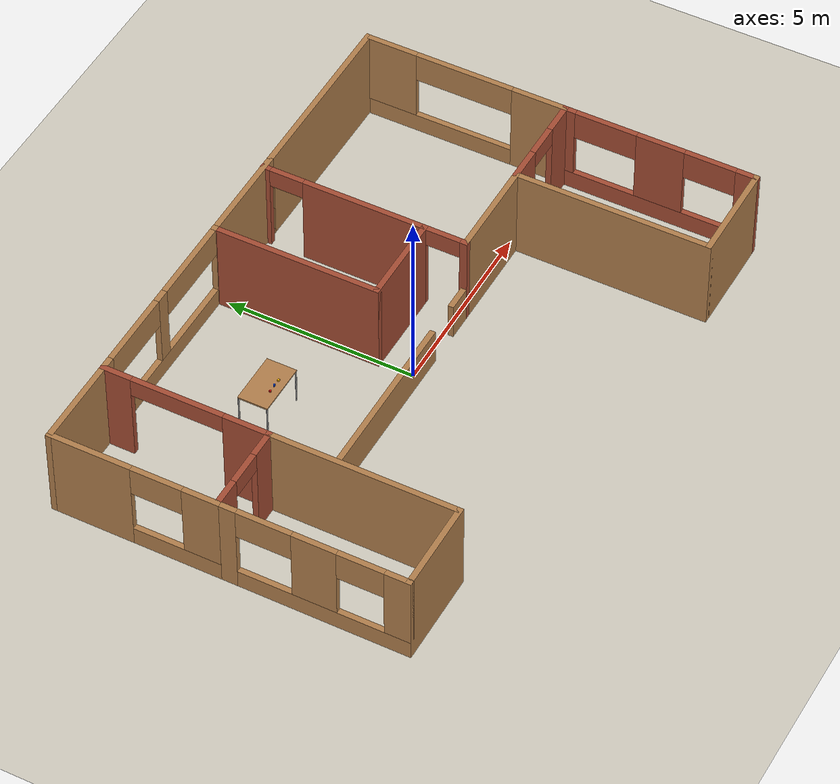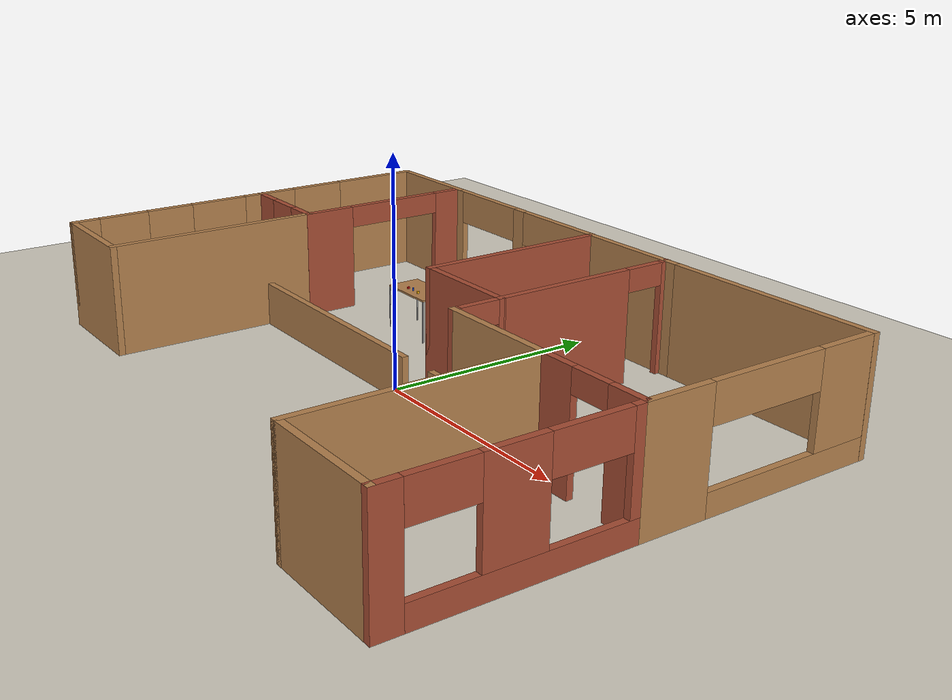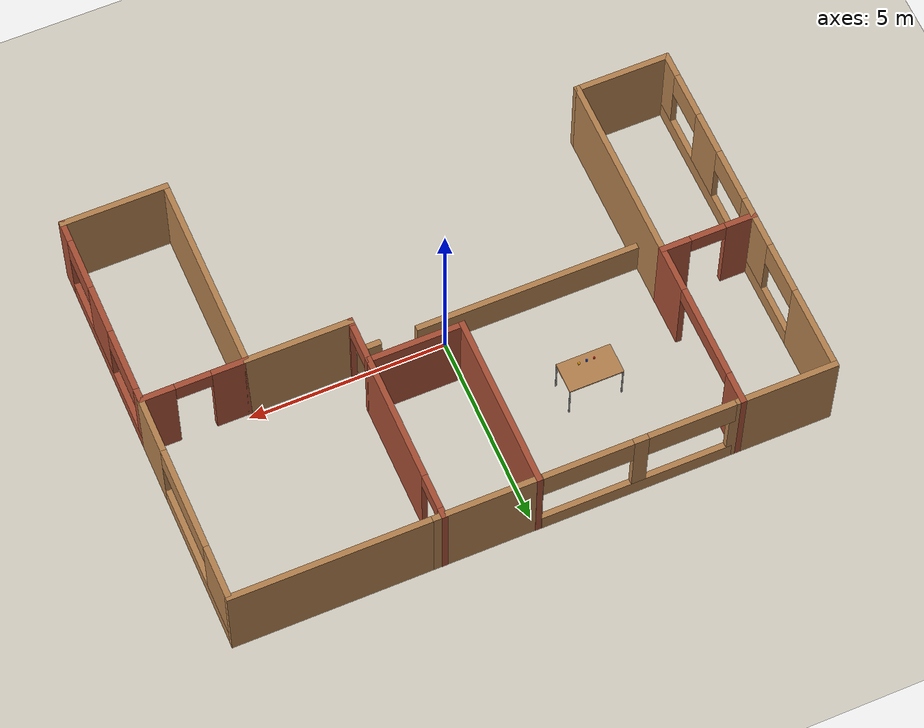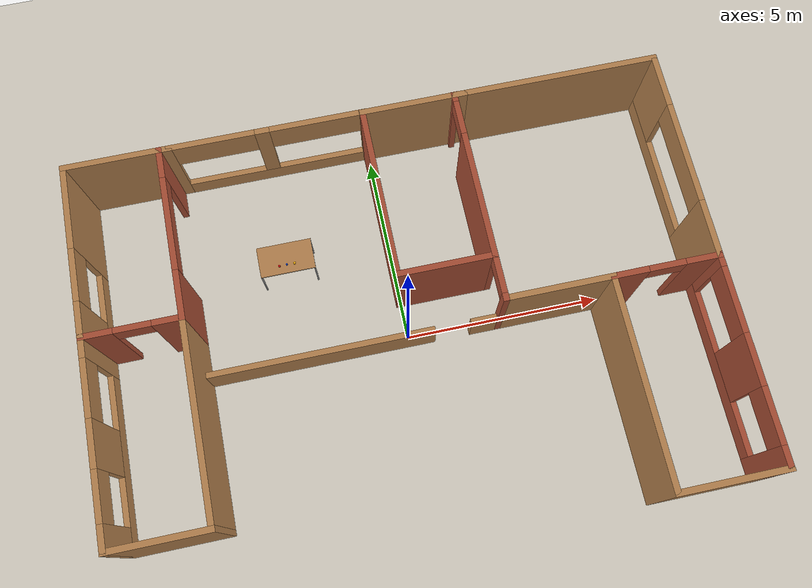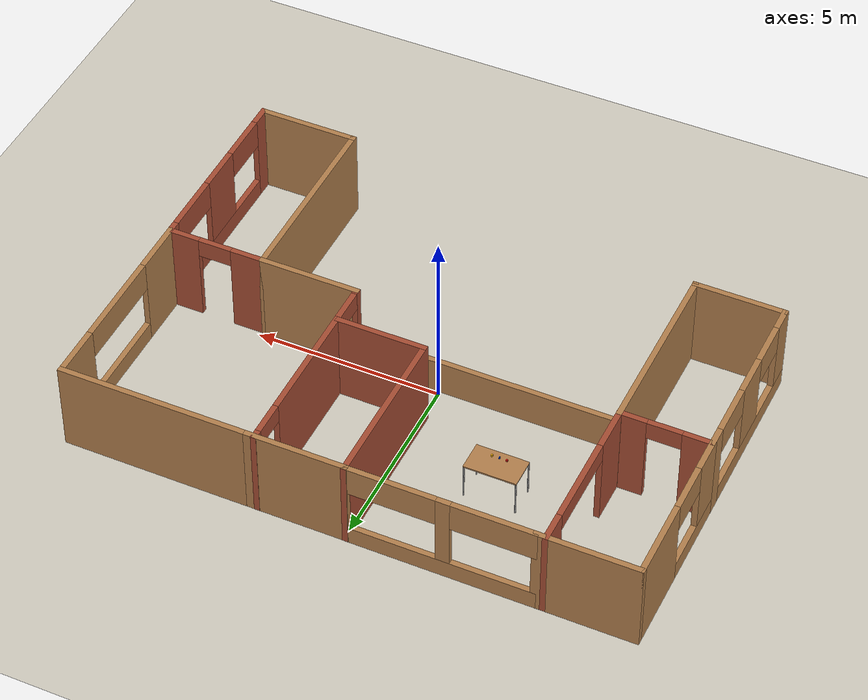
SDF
<sdf version="1.6"><world name="default"><physics name="default_physics" type="ode"><max_step_size>0.001</max_step_size><real_time_update_rate>1000</real_time_update_rate></physics><light name="sun" type="directional"><cast_shadows>true</cast_shadows><pose>0 0 10 0 0 0</pose><diffuse>.85 .82 .76 1</diffuse><specular>0.2 0.2 0.2 1</specular><direction>-.35 -.25 -.9</direction></light><model name="ground"><static>true</static><link name="ground"><collision name="ground"><geometry><plane><normal>0 0 1</normal><size>100 100</size></plane></geometry></collision><visual name="ground"><geometry><plane><normal>0 0 1</normal><size>30 24</size></plane></geometry><material><ambient>.76 .74 .69 1</ambient><diffuse>.82 .80 .75 1</diffuse><specular>.02 .02 .02 1</specular></material></visual></link></model><scene><ambient>.55 .55 .58 1</ambient><background>.75 .80 .86 1</background></scene><light name="soft_fill" type="directional"><cast_shadows>false</cast_shadows><diffuse>.28 .32 .38 1</diffuse><specular>.05 .05 .05 1</specular><direction>.5 .3 -.7</direction></light><model name="turtlebot3_house">
    <link name="Wall_101">
      <pose frame="">-0.05 3.1 0 0 0 -1.5708</pose>
      <self_collide>0</self_collide>
      <kinematic>0</kinematic>
      <visual name="Wall_101_Visual">
        <pose frame="">0 0 1.25 0 -0 0</pose>
        <geometry>
          <box>
            <size>4.5 0.15 2.5</size>
          </box>
        </geometry>
        <material>
          <script>
            <uri>file://media/materials/scripts/gazebo.material</uri>
            <name>Gazebo/Bricks</name>
          </script>
          <ambient>1 1 1 1</ambient>
          <diffuse>1 1 1 1</diffuse>
          <specular>0.2 0.2 0.2 1</specular>
          <emissive>0 0 0 1</emissive>
        </material>
        <cast_shadows>1</cast_shadows>
        <transparency>0</transparency>
      </visual>
      <collision name="Wall_101_Collision">
        <laser_retro>0</laser_retro>
        <max_contacts>10</max_contacts>
        <pose frame="">0 0 1.25 0 -0 0</pose>
        <geometry>
          <box>
            <size>4.5 0.15 2.5</size>
          </box>
        </geometry>
        <surface>
          <friction>
            <ode>
              <mu>1</mu>
              <mu2>1</mu2>
              <fdir1>0 0 0</fdir1>
              <slip1>0</slip1>
              <slip2>0</slip2>
            </ode>
            <torsional>
              <coefficient>1</coefficient>
              <patch_radius>0</patch_radius>
              <surface_radius>0</surface_radius>
              <use_patch_radius>1</use_patch_radius>
              <ode>
                <slip>0</slip>
              </ode>
            </torsional>
          </friction>
          <bounce>
            <restitution_coefficient>0</restitution_coefficient>
            <threshold>1e+06</threshold>
          </bounce>
          <contact>
            <collide_without_contact>0</collide_without_contact>
            <collide_without_contact_bitmask>1</collide_without_contact_bitmask>
            <collide_bitmask>1</collide_bitmask>
            <ode>
              <soft_cfm>0</soft_cfm>
              <soft_erp>0.2</soft_erp>
              <kp>1e+13</kp>
              <kd>1</kd>
              <max_vel>0.01</max_vel>
              <min_depth>0</min_depth>
            </ode>
            <bullet>
              <split_impulse>1</split_impulse>
              <split_impulse_penetration_threshold>-0.01</split_impulse_penetration_threshold>
              <soft_cfm>0</soft_cfm>
              <soft_erp>0.2</soft_erp>
              <kp>1e+13</kp>
              <kd>1</kd>
            </bullet>
          </contact>
        </surface>
      </collision>
    </link>
    <link name="Wall_104">
      <pose frame="">2.3 3.1 0 0 -0 1.5708</pose>
      <self_collide>0</self_collide>
      <kinematic>0</kinematic>
      <visual name="Wall_104_Visual_1">
        <pose frame="">2.11625 0 1.25 0 -0 0</pose>
        <geometry>
          <box>
            <size>0.267504 0.15 2.5</size>
          </box>
        </geometry>
        <material>
          <script>
            <uri>file://media/materials/scripts/gazebo.material</uri>
            <name>Gazebo/Bricks</name>
          </script>
          <ambient>1 1 1 1</ambient>
          <diffuse>1 1 1 1</diffuse>
          <specular>0.2 0.2 0.2 1</specular>
          <emissive>0 0 0 1</emissive>
        </material>
        <cast_shadows>1</cast_shadows>
        <transparency>0</transparency>
      </visual>
      <visual name="Wall_104_Visual_2">
        <pose frame="">1.5325 0 2.25 0 -0 0</pose>
        <geometry>
          <box>
            <size>0.9 0.15 0.5</size>
          </box>
        </geometry>
        <material>
          <script>
            <uri>file://media/materials/scripts/gazebo.material</uri>
            <name>Gazebo/Bricks</name>
          </script>
          <ambient>1 1 1 1</ambient>
          <diffuse>1 1 1 1</diffuse>
          <specular>0.2 0.2 0.2 1</specular>
          <emissive>0 0 0 1</emissive>
        </material>
        <cast_shadows>1</cast_shadows>
        <transparency>0</transparency>
      </visual>
      <visual name="Wall_104_Visual_0">
        <pose frame="">-0.583752 0 1.25 0 -0 0</pose>
        <geometry>
          <box>
            <size>3.3325 0.15 2.5</size>
          </box>
        </geometry>
        <material>
          <script>
            <uri>file://media/materials/scripts/gazebo.material</uri>
            <name>Gazebo/Bricks</name>
          </script>
          <ambient>1 1 1 1</ambient>
          <diffuse>1 1 1 1</diffuse>
          <specular>0.2 0.2 0.2 1</specular>
          <emissive>0 0 0 1</emissive>
        </material>
        <cast_shadows>1</cast_shadows>
        <transparency>0</transparency>
      </visual>
      <collision name="Wall_104_Collision_1">
        <laser_retro>0</laser_retro>
        <max_contacts>10</max_contacts>
        <pose frame="">2.11625 0 1.25 0 -0 0</pose>
        <geometry>
          <box>
            <size>0.267504 0.15 2.5</size>
          </box>
        </geometry>
        <surface>
          <friction>
            <ode>
              <mu>1</mu>
              <mu2>1</mu2>
              <fdir1>0 0 0</fdir1>
              <slip1>0</slip1>
              <slip2>0</slip2>
            </ode>
            <torsional>
              <coefficient>1</coefficient>
              <patch_radius>0</patch_radius>
              <surface_radius>0</surface_radius>
              <use_patch_radius>1</use_patch_radius>
              <ode>
                <slip>0</slip>
              </ode>
            </torsional>
          </friction>
          <bounce>
            <restitution_coefficient>0</restitution_coefficient>
            <threshold>1e+06</threshold>
          </bounce>
          <contact>
            <collide_without_contact>0</collide_without_contact>
            <collide_without_contact_bitmask>1</collide_without_contact_bitmask>
            <collide_bitmask>1</collide_bitmask>
            <ode>
              <soft_cfm>0</soft_cfm>
              <soft_erp>0.2</soft_erp>
              <kp>1e+13</kp>
              <kd>1</kd>
              <max_vel>0.01</max_vel>
              <min_depth>0</min_depth>
            </ode>
            <bullet>
              <split_impulse>1</split_impulse>
              <split_impulse_penetration_threshold>-0.01</split_impulse_penetration_threshold>
              <soft_cfm>0</soft_cfm>
              <soft_erp>0.2</soft_erp>
              <kp>1e+13</kp>
              <kd>1</kd>
            </bullet>
          </contact>
        </surface>
      </collision>
      <collision name="Wall_104_Collision_2">
        <laser_retro>0</laser_retro>
        <max_contacts>10</max_contacts>
        <pose frame="">1.5325 0 2.25 0 -0 0</pose>
        <geometry>
          <box>
            <size>0.9 0.15 0.5</size>
          </box>
        </geometry>
        <surface>
          <friction>
            <ode>
              <mu>1</mu>
              <mu2>1</mu2>
              <fdir1>0 0 0</fdir1>
              <slip1>0</slip1>
              <slip2>0</slip2>
            </ode>
            <torsional>
              <coefficient>1</coefficient>
              <patch_radius>0</patch_radius>
              <surface_radius>0</surface_radius>
              <use_patch_radius>1</use_patch_radius>
              <ode>
                <slip>0</slip>
              </ode>
            </torsional>
          </friction>
          <bounce>
            <restitution_coefficient>0</restitution_coefficient>
            <threshold>1e+06</threshold>
          </bounce>
          <contact>
            <collide_without_contact>0</collide_without_contact>
            <collide_without_contact_bitmask>1</collide_without_contact_bitmask>
            <collide_bitmask>1</collide_bitmask>
            <ode>
              <soft_cfm>0</soft_cfm>
              <soft_erp>0.2</soft_erp>
              <kp>1e+13</kp>
              <kd>1</kd>
              <max_vel>0.01</max_vel>
              <min_depth>0</min_depth>
            </ode>
            <bullet>
              <split_impulse>1</split_impulse>
              <split_impulse_penetration_threshold>-0.01</split_impulse_penetration_threshold>
              <soft_cfm>0</soft_cfm>
              <soft_erp>0.2</soft_erp>
              <kp>1e+13</kp>
              <kd>1</kd>
            </bullet>
          </contact>
        </surface>
      </collision>
      <collision name="Wall_104_Collision_0">
        <laser_retro>0</laser_retro>
        <max_contacts>10</max_contacts>
        <pose frame="">-0.583752 0 1.25 0 -0 0</pose>
        <geometry>
          <box>
            <size>3.3325 0.15 2.5</size>
          </box>
        </geometry>
        <surface>
          <friction>
            <ode>
              <mu>1</mu>
              <mu2>1</mu2>
              <fdir1>0 0 0</fdir1>
              <slip1>0</slip1>
              <slip2>0</slip2>
            </ode>
            <torsional>
              <coefficient>1</coefficient>
              <patch_radius>0</patch_radius>
              <surface_radius>0</surface_radius>
              <use_patch_radius>1</use_patch_radius>
              <ode>
                <slip>0</slip>
              </ode>
            </torsional>
          </friction>
          <bounce>
            <restitution_coefficient>0</restitution_coefficient>
            <threshold>1e+06</threshold>
          </bounce>
          <contact>
            <collide_without_contact>0</collide_without_contact>
            <collide_without_contact_bitmask>1</collide_without_contact_bitmask>
            <collide_bitmask>1</collide_bitmask>
            <ode>
              <soft_cfm>0</soft_cfm>
              <soft_erp>0.2</soft_erp>
              <kp>1e+13</kp>
              <kd>1</kd>
              <max_vel>0.01</max_vel>
              <min_depth>0</min_depth>
            </ode>
            <bullet>
              <split_impulse>1</split_impulse>
              <split_impulse_penetration_threshold>-0.01</split_impulse_penetration_threshold>
              <soft_cfm>0</soft_cfm>
              <soft_erp>0.2</soft_erp>
              <kp>1e+13</kp>
              <kd>1</kd>
            </bullet>
          </contact>
        </surface>
      </collision>
    </link>
    <link name="Wall_106">
      <pose frame="">6.2 -0.175 0 0 -0 0</pose>
      <self_collide>0</self_collide>
      <kinematic>0</kinematic>
      <visual name="Wall_106_Visual_1">
        <pose frame="">0.922235 0 1.25 0 -0 0</pose>
        <geometry>
          <box>
            <size>0.905529 0.15 2.5</size>
          </box>
        </geometry>
        <material>
          <script>
            <uri>file://media/materials/scripts/gazebo.material</uri>
            <name>Gazebo/Bricks</name>
          </script>
          <ambient>1 1 1 1</ambient>
          <diffuse>1 1 1 1</diffuse>
          <specular>0.2 0.2 0.2 1</specular>
          <emissive>0 0 0 1</emissive>
        </material>
        <cast_shadows>1</cast_shadows>
        <transparency>0</transparency>
      </visual>
      <visual name="Wall_106_Visual_2">
        <pose frame="">0.019471 0 2.25 0 -0 0</pose>
        <geometry>
          <box>
            <size>0.9 0.15 0.5</size>
          </box>
        </geometry>
        <material>
          <script>
            <uri>file://media/materials/scripts/gazebo.material</uri>
            <name>Gazebo/Bricks</name>
          </script>
          <ambient>1 1 1 1</ambient>
          <diffuse>1 1 1 1</diffuse>
          <specular>0.2 0.2 0.2 1</specular>
          <emissive>0 0 0 1</emissive>
        </material>
        <cast_shadows>1</cast_shadows>
        <transparency>0</transparency>
      </visual>
      <visual name="Wall_106_Visual_0">
        <pose frame="">-0.902765 0 1.25 0 -0 0</pose>
        <geometry>
          <box>
            <size>0.944471 0.15 2.5</size>
          </box>
        </geometry>
        <material>
          <script>
            <uri>file://media/materials/scripts/gazebo.material</uri>
            <name>Gazebo/Bricks</name>
          </script>
          <ambient>1 1 1 1</ambient>
          <diffuse>1 1 1 1</diffuse>
          <specular>0.2 0.2 0.2 1</specular>
          <emissive>0 0 0 1</emissive>
        </material>
        <cast_shadows>1</cast_shadows>
        <transparency>0</transparency>
      </visual>
      <collision name="Wall_106_Collision_1">
        <laser_retro>0</laser_retro>
        <max_contacts>10</max_contacts>
        <pose frame="">0.922235 0 1.25 0 -0 0</pose>
        <geometry>
          <box>
            <size>0.905529 0.15 2.5</size>
          </box>
        </geometry>
        <surface>
          <friction>
            <ode>
              <mu>1</mu>
              <mu2>1</mu2>
              <fdir1>0 0 0</fdir1>
              <slip1>0</slip1>
              <slip2>0</slip2>
            </ode>
            <torsional>
              <coefficient>1</coefficient>
              <patch_radius>0</patch_radius>
              <surface_radius>0</surface_radius>
              <use_patch_radius>1</use_patch_radius>
              <ode>
                <slip>0</slip>
              </ode>
            </torsional>
          </friction>
          <bounce>
            <restitution_coefficient>0</restitution_coefficient>
            <threshold>1e+06</threshold>
          </bounce>
          <contact>
            <collide_without_contact>0</collide_without_contact>
            <collide_without_contact_bitmask>1</collide_without_contact_bitmask>
            <collide_bitmask>1</collide_bitmask>
            <ode>
              <soft_cfm>0</soft_cfm>
              <soft_erp>0.2</soft_erp>
              <kp>1e+13</kp>
              <kd>1</kd>
              <max_vel>0.01</max_vel>
              <min_depth>0</min_depth>
            </ode>
            <bullet>
              <split_impulse>1</split_impulse>
              <split_impulse_penetration_threshold>-0.01</split_impulse_penetration_threshold>
              <soft_cfm>0</soft_cfm>
              <soft_erp>0.2</soft_erp>
              <kp>1e+13</kp>
              <kd>1</kd>
            </bullet>
          </contact>
        </surface>
      </collision>
      <collision name="Wall_106_Collision_0">
        <laser_retro>0</laser_retro>
        <max_contacts>10</max_contacts>
        <pose frame="">-0.902765 0 1.25 0 -0 0</pose>
        <geometry>
          <box>
            <size>0.944471 0.15 2.5</size>
          </box>
        </geometry>
        <surface>
          <friction>
            <ode>
              <mu>1</mu>
              <mu2>1</mu2>
              <fdir1>0 0 0</fdir1>
              <slip1>0</slip1>
              <slip2>0</slip2>
            </ode>
            <torsional>
              <coefficient>1</coefficient>
              <patch_radius>0</patch_radius>
              <surface_radius>0</surface_radius>
              <use_patch_radius>1</use_patch_radius>
              <ode>
                <slip>0</slip>
              </ode>
            </torsional>
          </friction>
          <bounce>
            <restitution_coefficient>0</restitution_coefficient>
            <threshold>1e+06</threshold>
          </bounce>
          <contact>
            <collide_without_contact>0</collide_without_contact>
            <collide_without_contact_bitmask>1</collide_without_contact_bitmask>
            <collide_bitmask>1</collide_bitmask>
            <ode>
              <soft_cfm>0</soft_cfm>
              <soft_erp>0.2</soft_erp>
              <kp>1e+13</kp>
              <kd>1</kd>
              <max_vel>0.01</max_vel>
              <min_depth>0</min_depth>
            </ode>
            <bullet>
              <split_impulse>1</split_impulse>
              <split_impulse_penetration_threshold>-0.01</split_impulse_penetration_threshold>
              <soft_cfm>0</soft_cfm>
              <soft_erp>0.2</soft_erp>
              <kp>1e+13</kp>
              <kd>1</kd>
            </bullet>
          </contact>
        </surface>
      </collision>
      <collision name="Wall_106_Collision_2">
        <laser_retro>0</laser_retro>
        <max_contacts>10</max_contacts>
        <pose frame="">0.019471 0 2.25 0 -0 0</pose>
        <geometry>
          <box>
            <size>0.9 0.15 0.5</size>
          </box>
        </geometry>
        <surface>
          <friction>
            <ode>
              <mu>1</mu>
              <mu2>1</mu2>
              <fdir1>0 0 0</fdir1>
              <slip1>0</slip1>
              <slip2>0</slip2>
            </ode>
            <torsional>
              <coefficient>1</coefficient>
              <patch_radius>0</patch_radius>
              <surface_radius>0</surface_radius>
              <use_patch_radius>1</use_patch_radius>
              <ode>
                <slip>0</slip>
              </ode>
            </torsional>
          </friction>
          <bounce>
            <restitution_coefficient>0</restitution_coefficient>
            <threshold>1e+06</threshold>
          </bounce>
          <contact>
            <collide_without_contact>0</collide_without_contact>
            <collide_without_contact_bitmask>1</collide_without_contact_bitmask>
            <collide_bitmask>1</collide_bitmask>
            <ode>
              <soft_cfm>0</soft_cfm>
              <soft_erp>0.2</soft_erp>
              <kp>1e+13</kp>
              <kd>1</kd>
              <max_vel>0.01</max_vel>
              <min_depth>0</min_depth>
            </ode>
            <bullet>
              <split_impulse>1</split_impulse>
              <split_impulse_penetration_threshold>-0.01</split_impulse_penetration_threshold>
              <soft_cfm>0</soft_cfm>
              <soft_erp>0.2</soft_erp>
              <kp>1e+13</kp>
              <kd>1</kd>
            </bullet>
          </contact>
        </surface>
      </collision>
    </link>
    <link name="Wall_108">
      <pose frame="">-1.37512 -0.17488 0 0 -0 0</pose>
      <self_collide>0</self_collide>
      <kinematic>0</kinematic>
      <visual name="Wall_108_Visual_0">
        <pose frame="">-0.856324 0 0.5 0 -0 0</pose>
        <geometry>
          <box>
            <size>5.78735 0.15 1</size>
          </box>
        </geometry>
        <material>
          <script>
            <uri>file://media/materials/scripts/gazebo.material</uri>
            <name>Gazebo/Wood</name>
          </script>
          <ambient>1 1 1 1</ambient>
          <diffuse>1 1 1 1</diffuse>
          <specular>0.2 0.2 0.2 1</specular>
          <emissive>0 0 0 1</emissive>
        </material>
        <cast_shadows>1</cast_shadows>
        <transparency>0</transparency>
      </visual>
      <visual name="Wall_108_Visual_1">
        <pose frame="">3.34368 0 0.5 0 -0 0</pose>
        <geometry>
          <box>
            <size>0.812647 0.15 1</size>
          </box>
        </geometry>
        <material>
          <script>
            <uri>file://media/materials/scripts/gazebo.material</uri>
            <name>Gazebo/Wood</name>
          </script>
          <ambient>1 1 1 1</ambient>
          <diffuse>1 1 1 1</diffuse>
          <specular>0.2 0.2 0.2 1</specular>
          <emissive>0 0 0 1</emissive>
        </material>
        <cast_shadows>1</cast_shadows>
        <transparency>0</transparency>
      </visual>
      <collision name="Wall_108_Collision_1">
        <laser_retro>0</laser_retro>
        <max_contacts>10</max_contacts>
        <pose frame="">3.34368 0 0.5 0 -0 0</pose>
        <geometry>
          <box>
            <size>0.812647 0.15 1</size>
          </box>
        </geometry>
        <surface>
          <friction>
            <ode>
              <mu>1</mu>
              <mu2>1</mu2>
              <fdir1>0 0 0</fdir1>
              <slip1>0</slip1>
              <slip2>0</slip2>
            </ode>
            <torsional>
              <coefficient>1</coefficient>
              <patch_radius>0</patch_radius>
              <surface_radius>0</surface_radius>
              <use_patch_radius>1</use_patch_radius>
              <ode>
                <slip>0</slip>
              </ode>
            </torsional>
          </friction>
          <bounce>
            <restitution_coefficient>0</restitution_coefficient>
            <threshold>1e+06</threshold>
          </bounce>
          <contact>
            <collide_without_contact>0</collide_without_contact>
            <collide_without_contact_bitmask>1</collide_without_contact_bitmask>
            <collide_bitmask>1</collide_bitmask>
            <ode>
              <soft_cfm>0</soft_cfm>
              <soft_erp>0.2</soft_erp>
              <kp>1e+13</kp>
              <kd>1</kd>
              <max_vel>0.01</max_vel>
              <min_depth>0</min_depth>
            </ode>
            <bullet>
              <split_impulse>1</split_impulse>
              <split_impulse_penetration_threshold>-0.01</split_impulse_penetration_threshold>
              <soft_cfm>0</soft_cfm>
              <soft_erp>0.2</soft_erp>
              <kp>1e+13</kp>
              <kd>1</kd>
            </bullet>
          </contact>
        </surface>
      </collision>
      <collision name="Wall_108_Collision_0">
        <laser_retro>0</laser_retro>
        <max_contacts>10</max_contacts>
        <pose frame="">-0.856324 0 0.5 0 -0 0</pose>
        <geometry>
          <box>
            <size>5.78735 0.15 1</size>
          </box>
        </geometry>
        <surface>
          <friction>
            <ode>
              <mu>1</mu>
              <mu2>1</mu2>
              <fdir1>0 0 0</fdir1>
              <slip1>0</slip1>
              <slip2>0</slip2>
            </ode>
            <torsional>
              <coefficient>1</coefficient>
              <patch_radius>0</patch_radius>
              <surface_radius>0</surface_radius>
              <use_patch_radius>1</use_patch_radius>
              <ode>
                <slip>0</slip>
              </ode>
            </torsional>
          </friction>
          <bounce>
            <restitution_coefficient>0</restitution_coefficient>
            <threshold>1e+06</threshold>
          </bounce>
          <contact>
            <collide_without_contact>0</collide_without_contact>
            <collide_without_contact_bitmask>1</collide_without_contact_bitmask>
            <collide_bitmask>1</collide_bitmask>
            <ode>
              <soft_cfm>0</soft_cfm>
              <soft_erp>0.2</soft_erp>
              <kp>1e+13</kp>
              <kd>1</kd>
              <max_vel>0.01</max_vel>
              <min_depth>0</min_depth>
            </ode>
            <bullet>
              <split_impulse>1</split_impulse>
              <split_impulse_penetration_threshold>-0.01</split_impulse_penetration_threshold>
              <soft_cfm>0</soft_cfm>
              <soft_erp>0.2</soft_erp>
              <kp>1e+13</kp>
              <kd>1</kd>
            </bullet>
          </contact>
        </surface>
      </collision>
    </link>
    <link name="Wall_81">
      <pose frame="">5.07752 5.2688 0 0 -0 3.14159</pose>
      <self_collide>0</self_collide>
      <kinematic>0</kinematic>
      <visual name="Wall_81_Visual">
        <pose frame="">0 0 1.25 0 -0 0</pose>
        <geometry>
          <box>
            <size>5 0.15 2.5</size>
          </box>
        </geometry>
        <material>
          <script>
            <uri>file://media/materials/scripts/gazebo.material</uri>
            <name>Gazebo/Wood</name>
          </script>
          <ambient>1 1 1 1</ambient>
          <diffuse>1 1 1 1</diffuse>
          <specular>0.2 0.2 0.2 1</specular>
          <emissive>0 0 0 1</emissive>
        </material>
        <cast_shadows>1</cast_shadows>
        <transparency>0</transparency>
      </visual>
      <collision name="Wall_81_Collision">
        <laser_retro>0</laser_retro>
        <max_contacts>10</max_contacts>
        <pose frame="">0 0 1.25 0 -0 0</pose>
        <geometry>
          <box>
            <size>5 0.15 2.5</size>
          </box>
        </geometry>
        <surface>
          <friction>
            <ode>
              <mu>1</mu>
              <mu2>1</mu2>
              <fdir1>0 0 0</fdir1>
              <slip1>0</slip1>
              <slip2>0</slip2>
            </ode>
            <torsional>
              <coefficient>1</coefficient>
              <patch_radius>0</patch_radius>
              <surface_radius>0</surface_radius>
              <use_patch_radius>1</use_patch_radius>
              <ode>
                <slip>0</slip>
              </ode>
            </torsional>
          </friction>
          <bounce>
            <restitution_coefficient>0</restitution_coefficient>
            <threshold>1e+06</threshold>
          </bounce>
          <contact>
            <collide_without_contact>0</collide_without_contact>
            <collide_without_contact_bitmask>1</collide_without_contact_bitmask>
            <collide_bitmask>1</collide_bitmask>
            <ode>
              <soft_cfm>0</soft_cfm>
              <soft_erp>0.2</soft_erp>
              <kp>1e+13</kp>
              <kd>1</kd>
              <max_vel>0.01</max_vel>
              <min_depth>0</min_depth>
            </ode>
            <bullet>
              <split_impulse>1</split_impulse>
              <split_impulse_penetration_threshold>-0.01</split_impulse_penetration_threshold>
              <soft_cfm>0</soft_cfm>
              <soft_erp>0.2</soft_erp>
              <kp>1e+13</kp>
              <kd>1</kd>
            </bullet>
          </contact>
        </surface>
      </collision>
    </link>
    <link name="Wall_82">
      <pose frame="">1.25 5.26876 0 0 -0 3.14159</pose>
      <self_collide>0</self_collide>
      <kinematic>0</kinematic>
      <visual name="Wall_82_Visual">
        <pose frame="">0 0 1.25 0 -0 0</pose>
        <geometry>
          <box>
            <size>2.75 0.15 2.5</size>
          </box>
        </geometry>
        <material>
          <script>
            <uri>file://media/materials/scripts/gazebo.material</uri>
            <name>Gazebo/Wood</name>
          </script>
          <ambient>1 1 1 1</ambient>
          <diffuse>1 1 1 1</diffuse>
          <specular>0.2 0.2 0.2 1</specular>
          <emissive>0 0 0 1</emissive>
        </material>
        <cast_shadows>1</cast_shadows>
        <transparency>0</transparency>
      </visual>
      <collision name="Wall_82_Collision">
        <laser_retro>0</laser_retro>
        <max_contacts>10</max_contacts>
        <pose frame="">0 0 1.25 0 -0 0</pose>
        <geometry>
          <box>
            <size>2.75 0.15 2.5</size>
          </box>
        </geometry>
        <surface>
          <friction>
            <ode>
              <mu>1</mu>
              <mu2>1</mu2>
              <fdir1>0 0 0</fdir1>
              <slip1>0</slip1>
              <slip2>0</slip2>
            </ode>
            <torsional>
              <coefficient>1</coefficient>
              <patch_radius>0</patch_radius>
              <surface_radius>0</surface_radius>
              <use_patch_radius>1</use_patch_radius>
              <ode>
                <slip>0</slip>
              </ode>
            </torsional>
          </friction>
          <bounce>
            <restitution_coefficient>0</restitution_coefficient>
            <threshold>1e+06</threshold>
          </bounce>
          <contact>
            <collide_without_contact>0</collide_without_contact>
            <collide_without_contact_bitmask>1</collide_without_contact_bitmask>
            <collide_bitmask>1</collide_bitmask>
            <ode>
              <soft_cfm>0</soft_cfm>
              <soft_erp>0.2</soft_erp>
              <kp>1e+13</kp>
              <kd>1</kd>
              <max_vel>0.01</max_vel>
              <min_depth>0</min_depth>
            </ode>
            <bullet>
              <split_impulse>1</split_impulse>
              <split_impulse_penetration_threshold>-0.01</split_impulse_penetration_threshold>
              <soft_cfm>0</soft_cfm>
              <soft_erp>0.2</soft_erp>
              <kp>1e+13</kp>
              <kd>1</kd>
            </bullet>
          </contact>
        </surface>
      </collision>
    </link>
    <link name="Wall_83">
      <pose frame="">-2.475 5.275 0 0 -0 3.14159</pose>
      <self_collide>0</self_collide>
      <kinematic>0</kinematic>
      <visual name="Wall_83_Visual_2">
        <pose frame="">0.110246 0 1.5 0 -0 0</pose>
        <geometry>
          <box>
            <size>0.37052 0.15 2</size>
          </box>
        </geometry>
        <material>
          <script>
            <uri>file://media/materials/scripts/gazebo.material</uri>
            <name>Gazebo/Wood</name>
          </script>
          <ambient>1 1 1 1</ambient>
          <diffuse>1 1 1 1</diffuse>
          <specular>0.2 0.2 0.2 1</specular>
          <emissive>0 0 0 1</emissive>
        </material>
        <cast_shadows>1</cast_shadows>
        <transparency>0</transparency>
      </visual>
      <visual name="Wall_83_Visual_6">
        <pose frame="">1.39775 0 2.1 0 -0 0</pose>
        <geometry>
          <box>
            <size>2.20449 0.15 0.8</size>
          </box>
        </geometry>
        <material>
          <script>
            <uri>file://media/materials/scripts/gazebo.material</uri>
            <name>Gazebo/Wood</name>
          </script>
          <ambient>1 1 1 1</ambient>
          <diffuse>1 1 1 1</diffuse>
          <specular>0.2 0.2 0.2 1</specular>
          <emissive>0 0 0 1</emissive>
        </material>
        <cast_shadows>1</cast_shadows>
        <transparency>0</transparency>
      </visual>
      <visual name="Wall_83_Visual_3">
        <pose frame="">0.110246 0 1.5 0 -0 0</pose>
        <geometry>
          <box>
            <size>0.37052 0.15 2</size>
          </box>
        </geometry>
        <material>
          <script>
            <uri>file://media/materials/scripts/gazebo.material</uri>
            <name>Gazebo/Wood</name>
          </script>
          <ambient>1 1 1 1</ambient>
          <diffuse>1 1 1 1</diffuse>
          <specular>0.2 0.2 0.2 1</specular>
          <emissive>0 0 0 1</emissive>
        </material>
        <cast_shadows>1</cast_shadows>
        <transparency>0</transparency>
      </visual>
      <visual name="Wall_83_Visual_1">
        <pose frame="">0.080993 0 0.25 0 -0 0</pose>
        <geometry>
          <box>
            <size>4.83801 0.15 0.5</size>
          </box>
        </geometry>
        <material>
          <script>
            <uri>file://media/materials/scripts/gazebo.material</uri>
            <name>Gazebo/Wood</name>
          </script>
          <ambient>1 1 1 1</ambient>
          <diffuse>1 1 1 1</diffuse>
          <specular>0.2 0.2 0.2 1</specular>
          <emissive>0 0 0 1</emissive>
        </material>
        <cast_shadows>1</cast_shadows>
        <transparency>0</transparency>
      </visual>
      <visual name="Wall_83_Visual_4">
        <pose frame="">-1.20651 0 2.1 0 -0 0</pose>
        <geometry>
          <box>
            <size>2.263 0.15 0.8</size>
          </box>
        </geometry>
        <material>
          <script>
            <uri>file://media/materials/scripts/gazebo.material</uri>
            <name>Gazebo/Wood</name>
          </script>
          <ambient>1 1 1 1</ambient>
          <diffuse>1 1 1 1</diffuse>
          <specular>0.2 0.2 0.2 1</specular>
          <emissive>0 0 0 1</emissive>
        </material>
        <cast_shadows>1</cast_shadows>
        <transparency>0</transparency>
      </visual>
      <visual name="Wall_83_Visual_5">
        <pose frame="">1.39775 0 2.1 0 -0 0</pose>
        <geometry>
          <box>
            <size>2.20449 0.15 0.8</size>
          </box>
        </geometry>
        <material>
          <script>
            <uri>file://media/materials/scripts/gazebo.material</uri>
            <name>Gazebo/Wood</name>
          </script>
          <ambient>1 1 1 1</ambient>
          <diffuse>1 1 1 1</diffuse>
          <specular>0.2 0.2 0.2 1</specular>
          <emissive>0 0 0 1</emissive>
        </material>
        <cast_shadows>1</cast_shadows>
        <transparency>0</transparency>
      </visual>
      <visual name="Wall_83_Visual_0">
        <pose frame="">-2.41901 0 1.25 0 -0 0</pose>
        <geometry>
          <box>
            <size>0.161986 0.15 2.5</size>
          </box>
        </geometry>
        <material>
          <script>
            <uri>file://media/materials/scripts/gazebo.material</uri>
            <name>Gazebo/Wood</name>
          </script>
          <ambient>1 1 1 1</ambient>
          <diffuse>1 1 1 1</diffuse>
          <specular>0.2 0.2 0.2 1</specular>
          <emissive>0 0 0 1</emissive>
        </material>
        <cast_shadows>1</cast_shadows>
        <transparency>0</transparency>
      </visual>
      <collision name="Wall_83_Collision_4">
        <laser_retro>0</laser_retro>
        <max_contacts>10</max_contacts>
        <pose frame="">-1.20651 0 2.1 0 -0 0</pose>
        <geometry>
          <box>
            <size>2.263 0.15 0.8</size>
          </box>
        </geometry>
        <surface>
          <friction>
            <ode>
              <mu>1</mu>
              <mu2>1</mu2>
              <fdir1>0 0 0</fdir1>
              <slip1>0</slip1>
              <slip2>0</slip2>
            </ode>
            <torsional>
              <coefficient>1</coefficient>
              <patch_radius>0</patch_radius>
              <surface_radius>0</surface_radius>
              <use_patch_radius>1</use_patch_radius>
              <ode>
                <slip>0</slip>
              </ode>
            </torsional>
          </friction>
          <bounce>
            <restitution_coefficient>0</restitution_coefficient>
            <threshold>1e+06</threshold>
          </bounce>
          <contact>
            <collide_without_contact>0</collide_without_contact>
            <collide_without_contact_bitmask>1</collide_without_contact_bitmask>
            <collide_bitmask>1</collide_bitmask>
            <ode>
              <soft_cfm>0</soft_cfm>
              <soft_erp>0.2</soft_erp>
              <kp>1e+13</kp>
              <kd>1</kd>
              <max_vel>0.01</max_vel>
              <min_depth>0</min_depth>
            </ode>
            <bullet>
              <split_impulse>1</split_impulse>
              <split_impulse_penetration_threshold>-0.01</split_impulse_penetration_threshold>
              <soft_cfm>0</soft_cfm>
              <soft_erp>0.2</soft_erp>
              <kp>1e+13</kp>
              <kd>1</kd>
            </bullet>
          </contact>
        </surface>
      </collision>
      <collision name="Wall_83_Collision_2">
        <laser_retro>0</laser_retro>
        <max_contacts>10</max_contacts>
        <pose frame="">0.110246 0 1.5 0 -0 0</pose>
        <geometry>
          <box>
            <size>0.37052 0.15 2</size>
          </box>
        </geometry>
        <surface>
          <friction>
            <ode>
              <mu>1</mu>
              <mu2>1</mu2>
              <fdir1>0 0 0</fdir1>
              <slip1>0</slip1>
              <slip2>0</slip2>
            </ode>
            <torsional>
              <coefficient>1</coefficient>
              <patch_radius>0</patch_radius>
              <surface_radius>0</surface_radius>
              <use_patch_radius>1</use_patch_radius>
              <ode>
                <slip>0</slip>
              </ode>
            </torsional>
          </friction>
          <bounce>
            <restitution_coefficient>0</restitution_coefficient>
            <threshold>1e+06</threshold>
          </bounce>
          <contact>
            <collide_without_contact>0</collide_without_contact>
            <collide_without_contact_bitmask>1</collide_without_contact_bitmask>
            <collide_bitmask>1</collide_bitmask>
            <ode>
              <soft_cfm>0</soft_cfm>
              <soft_erp>0.2</soft_erp>
              <kp>1e+13</kp>
              <kd>1</kd>
              <max_vel>0.01</max_vel>
              <min_depth>0</min_depth>
            </ode>
            <bullet>
              <split_impulse>1</split_impulse>
              <split_impulse_penetration_threshold>-0.01</split_impulse_penetration_threshold>
              <soft_cfm>0</soft_cfm>
              <soft_erp>0.2</soft_erp>
              <kp>1e+13</kp>
              <kd>1</kd>
            </bullet>
          </contact>
        </surface>
      </collision>
      <collision name="Wall_83_Collision_6">
        <laser_retro>0</laser_retro>
        <max_contacts>10</max_contacts>
        <pose frame="">1.39775 0 2.1 0 -0 0</pose>
        <geometry>
          <box>
            <size>2.20449 0.15 0.8</size>
          </box>
        </geometry>
        <surface>
          <friction>
            <ode>
              <mu>1</mu>
              <mu2>1</mu2>
              <fdir1>0 0 0</fdir1>
              <slip1>0</slip1>
              <slip2>0</slip2>
            </ode>
            <torsional>
              <coefficient>1</coefficient>
              <patch_radius>0</patch_radius>
              <surface_radius>0</surface_radius>
              <use_patch_radius>1</use_patch_radius>
              <ode>
                <slip>0</slip>
              </ode>
            </torsional>
          </friction>
          <bounce>
            <restitution_coefficient>0</restitution_coefficient>
            <threshold>1e+06</threshold>
          </bounce>
          <contact>
            <collide_without_contact>0</collide_without_contact>
            <collide_without_contact_bitmask>1</collide_without_contact_bitmask>
            <collide_bitmask>1</collide_bitmask>
            <ode>
              <soft_cfm>0</soft_cfm>
              <soft_erp>0.2</soft_erp>
              <kp>1e+13</kp>
              <kd>1</kd>
              <max_vel>0.01</max_vel>
              <min_depth>0</min_depth>
            </ode>
            <bullet>
              <split_impulse>1</split_impulse>
              <split_impulse_penetration_threshold>-0.01</split_impulse_penetration_threshold>
              <soft_cfm>0</soft_cfm>
              <soft_erp>0.2</soft_erp>
              <kp>1e+13</kp>
              <kd>1</kd>
            </bullet>
          </contact>
        </surface>
      </collision>
      <collision name="Wall_83_Collision_0">
        <laser_retro>0</laser_retro>
        <max_contacts>10</max_contacts>
        <pose frame="">-2.41901 0 1.25 0 -0 0</pose>
        <geometry>
          <box>
            <size>0.161986 0.15 2.5</size>
          </box>
        </geometry>
        <surface>
          <friction>
            <ode>
              <mu>1</mu>
              <mu2>1</mu2>
              <fdir1>0 0 0</fdir1>
              <slip1>0</slip1>
              <slip2>0</slip2>
            </ode>
            <torsional>
              <coefficient>1</coefficient>
              <patch_radius>0</patch_radius>
              <surface_radius>0</surface_radius>
              <use_patch_radius>1</use_patch_radius>
              <ode>
                <slip>0</slip>
              </ode>
            </torsional>
          </friction>
          <bounce>
            <restitution_coefficient>0</restitution_coefficient>
            <threshold>1e+06</threshold>
          </bounce>
          <contact>
            <collide_without_contact>0</collide_without_contact>
            <collide_without_contact_bitmask>1</collide_without_contact_bitmask>
            <collide_bitmask>1</collide_bitmask>
            <ode>
              <soft_cfm>0</soft_cfm>
              <soft_erp>0.2</soft_erp>
              <kp>1e+13</kp>
              <kd>1</kd>
              <max_vel>0.01</max_vel>
              <min_depth>0</min_depth>
            </ode>
            <bullet>
              <split_impulse>1</split_impulse>
              <split_impulse_penetration_threshold>-0.01</split_impulse_penetration_threshold>
              <soft_cfm>0</soft_cfm>
              <soft_erp>0.2</soft_erp>
              <kp>1e+13</kp>
              <kd>1</kd>
            </bullet>
          </contact>
        </surface>
      </collision>
      <collision name="Wall_83_Collision_1">
        <laser_retro>0</laser_retro>
        <max_contacts>10</max_contacts>
        <pose frame="">0.080993 0 0.25 0 -0 0</pose>
        <geometry>
          <box>
            <size>4.83801 0.15 0.5</size>
          </box>
        </geometry>
        <surface>
          <friction>
            <ode>
              <mu>1</mu>
              <mu2>1</mu2>
              <fdir1>0 0 0</fdir1>
              <slip1>0</slip1>
              <slip2>0</slip2>
            </ode>
            <torsional>
              <coefficient>1</coefficient>
              <patch_radius>0</patch_radius>
              <surface_radius>0</surface_radius>
              <use_patch_radius>1</use_patch_radius>
              <ode>
                <slip>0</slip>
              </ode>
            </torsional>
          </friction>
          <bounce>
            <restitution_coefficient>0</restitution_coefficient>
            <threshold>1e+06</threshold>
          </bounce>
          <contact>
            <collide_without_contact>0</collide_without_contact>
            <collide_without_contact_bitmask>1</collide_without_contact_bitmask>
            <collide_bitmask>1</collide_bitmask>
            <ode>
              <soft_cfm>0</soft_cfm>
              <soft_erp>0.2</soft_erp>
              <kp>1e+13</kp>
              <kd>1</kd>
              <max_vel>0.01</max_vel>
              <min_depth>0</min_depth>
            </ode>
            <bullet>
              <split_impulse>1</split_impulse>
              <split_impulse_penetration_threshold>-0.01</split_impulse_penetration_threshold>
              <soft_cfm>0</soft_cfm>
              <soft_erp>0.2</soft_erp>
              <kp>1e+13</kp>
              <kd>1</kd>
            </bullet>
          </contact>
        </surface>
      </collision>
      <collision name="Wall_83_Collision_3">
        <laser_retro>0</laser_retro>
        <max_contacts>10</max_contacts>
        <pose frame="">0.110246 0 1.5 0 -0 0</pose>
        <geometry>
          <box>
            <size>0.37052 0.15 2</size>
          </box>
        </geometry>
        <surface>
          <friction>
            <ode>
              <mu>1</mu>
              <mu2>1</mu2>
              <fdir1>0 0 0</fdir1>
              <slip1>0</slip1>
              <slip2>0</slip2>
            </ode>
            <torsional>
              <coefficient>1</coefficient>
              <patch_radius>0</patch_radius>
              <surface_radius>0</surface_radius>
              <use_patch_radius>1</use_patch_radius>
              <ode>
                <slip>0</slip>
              </ode>
            </torsional>
          </friction>
          <bounce>
            <restitution_coefficient>0</restitution_coefficient>
            <threshold>1e+06</threshold>
          </bounce>
          <contact>
            <collide_without_contact>0</collide_without_contact>
            <collide_without_contact_bitmask>1</collide_without_contact_bitmask>
            <collide_bitmask>1</collide_bitmask>
            <ode>
              <soft_cfm>0</soft_cfm>
              <soft_erp>0.2</soft_erp>
              <kp>1e+13</kp>
              <kd>1</kd>
              <max_vel>0.01</max_vel>
              <min_depth>0</min_depth>
            </ode>
            <bullet>
              <split_impulse>1</split_impulse>
              <split_impulse_penetration_threshold>-0.01</split_impulse_penetration_threshold>
              <soft_cfm>0</soft_cfm>
              <soft_erp>0.2</soft_erp>
              <kp>1e+13</kp>
              <kd>1</kd>
            </bullet>
          </contact>
        </surface>
      </collision>
      <collision name="Wall_83_Collision_5">
        <laser_retro>0</laser_retro>
        <max_contacts>10</max_contacts>
        <pose frame="">1.39775 0 2.1 0 -0 0</pose>
        <geometry>
          <box>
            <size>2.20449 0.15 0.8</size>
          </box>
        </geometry>
        <surface>
          <friction>
            <ode>
              <mu>1</mu>
              <mu2>1</mu2>
              <fdir1>0 0 0</fdir1>
              <slip1>0</slip1>
              <slip2>0</slip2>
            </ode>
            <torsional>
              <coefficient>1</coefficient>
              <patch_radius>0</patch_radius>
              <surface_radius>0</surface_radius>
              <use_patch_radius>1</use_patch_radius>
              <ode>
                <slip>0</slip>
              </ode>
            </torsional>
          </friction>
          <bounce>
            <restitution_coefficient>0</restitution_coefficient>
            <threshold>1e+06</threshold>
          </bounce>
          <contact>
            <collide_without_contact>0</collide_without_contact>
            <collide_without_contact_bitmask>1</collide_without_contact_bitmask>
            <collide_bitmask>1</collide_bitmask>
            <ode>
              <soft_cfm>0</soft_cfm>
              <soft_erp>0.2</soft_erp>
              <kp>1e+13</kp>
              <kd>1</kd>
              <max_vel>0.01</max_vel>
              <min_depth>0</min_depth>
            </ode>
            <bullet>
              <split_impulse>1</split_impulse>
              <split_impulse_penetration_threshold>-0.01</split_impulse_penetration_threshold>
              <soft_cfm>0</soft_cfm>
              <soft_erp>0.2</soft_erp>
              <kp>1e+13</kp>
              <kd>1</kd>
            </bullet>
          </contact>
        </surface>
      </collision>
    </link>
    <link name="Wall_84">
      <pose frame="">-6.2 5.275 0 0 -0 3.14159</pose>
      <self_collide>0</self_collide>
      <kinematic>0</kinematic>
      <visual name="Wall_84_Visual">
        <pose frame="">0 0 1.25 0 -0 0</pose>
        <geometry>
          <box>
            <size>2.75 0.15 2.5</size>
          </box>
        </geometry>
        <material>
          <script>
            <uri>file://media/materials/scripts/gazebo.material</uri>
            <name>Gazebo/Wood</name>
          </script>
          <ambient>1 1 1 1</ambient>
          <diffuse>1 1 1 1</diffuse>
          <specular>0.2 0.2 0.2 1</specular>
          <emissive>0 0 0 1</emissive>
        </material>
        <cast_shadows>1</cast_shadows>
        <transparency>0</transparency>
      </visual>
      <collision name="Wall_84_Collision">
        <laser_retro>0</laser_retro>
        <max_contacts>10</max_contacts>
        <pose frame="">0 0 1.25 0 -0 0</pose>
        <geometry>
          <box>
            <size>2.75 0.15 2.5</size>
          </box>
        </geometry>
        <surface>
          <friction>
            <ode>
              <mu>1</mu>
              <mu2>1</mu2>
              <fdir1>0 0 0</fdir1>
              <slip1>0</slip1>
              <slip2>0</slip2>
            </ode>
            <torsional>
              <coefficient>1</coefficient>
              <patch_radius>0</patch_radius>
              <surface_radius>0</surface_radius>
              <use_patch_radius>1</use_patch_radius>
              <ode>
                <slip>0</slip>
              </ode>
            </torsional>
          </friction>
          <bounce>
            <restitution_coefficient>0</restitution_coefficient>
            <threshold>1e+06</threshold>
          </bounce>
          <contact>
            <collide_without_contact>0</collide_without_contact>
            <collide_without_contact_bitmask>1</collide_without_contact_bitmask>
            <collide_bitmask>1</collide_bitmask>
            <ode>
              <soft_cfm>0</soft_cfm>
              <soft_erp>0.2</soft_erp>
              <kp>1e+13</kp>
              <kd>1</kd>
              <max_vel>0.01</max_vel>
              <min_depth>0</min_depth>
            </ode>
            <bullet>
              <split_impulse>1</split_impulse>
              <split_impulse_penetration_threshold>-0.01</split_impulse_penetration_threshold>
              <soft_cfm>0</soft_cfm>
              <soft_erp>0.2</soft_erp>
              <kp>1e+13</kp>
              <kd>1</kd>
            </bullet>
          </contact>
        </surface>
      </collision>
    </link>
    <link name="Wall_85">
      <pose frame="">-7.5 3.1 0 0 0 -1.5708</pose>
      <self_collide>0</self_collide>
      <kinematic>0</kinematic>
      <visual name="Wall_85_Visual_3">
        <pose frame="">0.62212 0 2.1 0 -0 0</pose>
        <geometry>
          <box>
            <size>1.332 0.15 0.8</size>
          </box>
        </geometry>
        <material>
          <script>
            <uri>file://media/materials/scripts/gazebo.material</uri>
            <name>Gazebo/Wood</name>
          </script>
          <ambient>1 1 1 1</ambient>
          <diffuse>1 1 1 1</diffuse>
          <specular>0.2 0.2 0.2 1</specular>
          <emissive>0 0 0 1</emissive>
        </material>
        <cast_shadows>1</cast_shadows>
        <transparency>0</transparency>
      </visual>
      <visual name="Wall_85_Visual_2">
        <pose frame="">1.76906 0 1.5 0 -0 0</pose>
        <geometry>
          <box>
            <size>0.96188 0.15 2</size>
          </box>
        </geometry>
        <material>
          <script>
            <uri>file://media/materials/scripts/gazebo.material</uri>
            <name>Gazebo/Wood</name>
          </script>
          <ambient>1 1 1 1</ambient>
          <diffuse>1 1 1 1</diffuse>
          <specular>0.2 0.2 0.2 1</specular>
          <emissive>0 0 0 1</emissive>
        </material>
        <cast_shadows>1</cast_shadows>
        <transparency>0</transparency>
      </visual>
      <visual name="Wall_85_Visual_0">
        <pose frame="">-1.14694 0 1.25 0 -0 0</pose>
        <geometry>
          <box>
            <size>2.20612 0.15 2.5</size>
          </box>
        </geometry>
        <material>
          <script>
            <uri>file://media/materials/scripts/gazebo.material</uri>
            <name>Gazebo/Wood</name>
          </script>
          <ambient>1 1 1 1</ambient>
          <diffuse>1 1 1 1</diffuse>
          <specular>0.2 0.2 0.2 1</specular>
          <emissive>0 0 0 1</emissive>
        </material>
        <cast_shadows>1</cast_shadows>
        <transparency>0</transparency>
      </visual>
      <visual name="Wall_85_Visual_1">
        <pose frame="">1.10306 0 0.25 0 -0 0</pose>
        <geometry>
          <box>
            <size>2.29388 0.15 0.5</size>
          </box>
        </geometry>
        <material>
          <script>
            <uri>file://media/materials/scripts/gazebo.material</uri>
            <name>Gazebo/Wood</name>
          </script>
          <ambient>1 1 1 1</ambient>
          <diffuse>1 1 1 1</diffuse>
          <specular>0.2 0.2 0.2 1</specular>
          <emissive>0 0 0 1</emissive>
        </material>
        <cast_shadows>1</cast_shadows>
        <transparency>0</transparency>
      </visual>
      <collision name="Wall_85_Collision_3">
        <laser_retro>0</laser_retro>
        <max_contacts>10</max_contacts>
        <pose frame="">0.62212 0 2.1 0 -0 0</pose>
        <geometry>
          <box>
            <size>1.332 0.15 0.8</size>
          </box>
        </geometry>
        <surface>
          <friction>
            <ode>
              <mu>1</mu>
              <mu2>1</mu2>
              <fdir1>0 0 0</fdir1>
              <slip1>0</slip1>
              <slip2>0</slip2>
            </ode>
            <torsional>
              <coefficient>1</coefficient>
              <patch_radius>0</patch_radius>
              <surface_radius>0</surface_radius>
              <use_patch_radius>1</use_patch_radius>
              <ode>
                <slip>0</slip>
              </ode>
            </torsional>
          </friction>
          <bounce>
            <restitution_coefficient>0</restitution_coefficient>
            <threshold>1e+06</threshold>
          </bounce>
          <contact>
            <collide_without_contact>0</collide_without_contact>
            <collide_without_contact_bitmask>1</collide_without_contact_bitmask>
            <collide_bitmask>1</collide_bitmask>
            <ode>
              <soft_cfm>0</soft_cfm>
              <soft_erp>0.2</soft_erp>
              <kp>1e+13</kp>
              <kd>1</kd>
              <max_vel>0.01</max_vel>
              <min_depth>0</min_depth>
            </ode>
            <bullet>
              <split_impulse>1</split_impulse>
              <split_impulse_penetration_threshold>-0.01</split_impulse_penetration_threshold>
              <soft_cfm>0</soft_cfm>
              <soft_erp>0.2</soft_erp>
              <kp>1e+13</kp>
              <kd>1</kd>
            </bullet>
          </contact>
        </surface>
      </collision>
      <collision name="Wall_85_Collision_2">
        <laser_retro>0</laser_retro>
        <max_contacts>10</max_contacts>
        <pose frame="">1.76906 0 1.5 0 -0 0</pose>
        <geometry>
          <box>
            <size>0.96188 0.15 2</size>
          </box>
        </geometry>
        <surface>
          <friction>
            <ode>
              <mu>1</mu>
              <mu2>1</mu2>
              <fdir1>0 0 0</fdir1>
              <slip1>0</slip1>
              <slip2>0</slip2>
            </ode>
            <torsional>
              <coefficient>1</coefficient>
              <patch_radius>0</patch_radius>
              <surface_radius>0</surface_radius>
              <use_patch_radius>1</use_patch_radius>
              <ode>
                <slip>0</slip>
              </ode>
            </torsional>
          </friction>
          <bounce>
            <restitution_coefficient>0</restitution_coefficient>
            <threshold>1e+06</threshold>
          </bounce>
          <contact>
            <collide_without_contact>0</collide_without_contact>
            <collide_without_contact_bitmask>1</collide_without_contact_bitmask>
            <collide_bitmask>1</collide_bitmask>
            <ode>
              <soft_cfm>0</soft_cfm>
              <soft_erp>0.2</soft_erp>
              <kp>1e+13</kp>
              <kd>1</kd>
              <max_vel>0.01</max_vel>
              <min_depth>0</min_depth>
            </ode>
            <bullet>
              <split_impulse>1</split_impulse>
              <split_impulse_penetration_threshold>-0.01</split_impulse_penetration_threshold>
              <soft_cfm>0</soft_cfm>
              <soft_erp>0.2</soft_erp>
              <kp>1e+13</kp>
              <kd>1</kd>
            </bullet>
          </contact>
        </surface>
      </collision>
      <collision name="Wall_85_Collision_1">
        <laser_retro>0</laser_retro>
        <max_contacts>10</max_contacts>
        <pose frame="">1.10306 0 0.25 0 -0 0</pose>
        <geometry>
          <box>
            <size>2.29388 0.15 0.5</size>
          </box>
        </geometry>
        <surface>
          <friction>
            <ode>
              <mu>1</mu>
              <mu2>1</mu2>
              <fdir1>0 0 0</fdir1>
              <slip1>0</slip1>
              <slip2>0</slip2>
            </ode>
            <torsional>
              <coefficient>1</coefficient>
              <patch_radius>0</patch_radius>
              <surface_radius>0</surface_radius>
              <use_patch_radius>1</use_patch_radius>
              <ode>
                <slip>0</slip>
              </ode>
            </torsional>
          </friction>
          <bounce>
            <restitution_coefficient>0</restitution_coefficient>
            <threshold>1e+06</threshold>
          </bounce>
          <contact>
            <collide_without_contact>0</collide_without_contact>
            <collide_without_contact_bitmask>1</collide_without_contact_bitmask>
            <collide_bitmask>1</collide_bitmask>
            <ode>
              <soft_cfm>0</soft_cfm>
              <soft_erp>0.2</soft_erp>
              <kp>1e+13</kp>
              <kd>1</kd>
              <max_vel>0.01</max_vel>
              <min_depth>0</min_depth>
            </ode>
            <bullet>
              <split_impulse>1</split_impulse>
              <split_impulse_penetration_threshold>-0.01</split_impulse_penetration_threshold>
              <soft_cfm>0</soft_cfm>
              <soft_erp>0.2</soft_erp>
              <kp>1e+13</kp>
              <kd>1</kd>
            </bullet>
          </contact>
        </surface>
      </collision>
      <collision name="Wall_85_Collision_0">
        <laser_retro>0</laser_retro>
        <max_contacts>10</max_contacts>
        <pose frame="">-1.14694 0 1.25 0 -0 0</pose>
        <geometry>
          <box>
            <size>2.20612 0.15 2.5</size>
          </box>
        </geometry>
        <surface>
          <friction>
            <ode>
              <mu>1</mu>
              <mu2>1</mu2>
              <fdir1>0 0 0</fdir1>
              <slip1>0</slip1>
              <slip2>0</slip2>
            </ode>
            <torsional>
              <coefficient>1</coefficient>
              <patch_radius>0</patch_radius>
              <surface_radius>0</surface_radius>
              <use_patch_radius>1</use_patch_radius>
              <ode>
                <slip>0</slip>
              </ode>
            </torsional>
          </friction>
          <bounce>
            <restitution_coefficient>0</restitution_coefficient>
            <threshold>1e+06</threshold>
          </bounce>
          <contact>
            <collide_without_contact>0</collide_without_contact>
            <collide_without_contact_bitmask>1</collide_without_contact_bitmask>
            <collide_bitmask>1</collide_bitmask>
            <ode>
              <soft_cfm>0</soft_cfm>
              <soft_erp>0.2</soft_erp>
              <kp>1e+13</kp>
              <kd>1</kd>
              <max_vel>0.01</max_vel>
              <min_depth>0</min_depth>
            </ode>
            <bullet>
              <split_impulse>1</split_impulse>
              <split_impulse_penetration_threshold>-0.01</split_impulse_penetration_threshold>
              <soft_cfm>0</soft_cfm>
              <soft_erp>0.2</soft_erp>
              <kp>1e+13</kp>
              <kd>1</kd>
            </bullet>
          </contact>
        </surface>
      </collision>
    </link>
    <link name="Wall_86">
      <pose frame="">-7.5 -1.5 0 0 0 -1.5708</pose>
      <self_collide>0</self_collide>
      <kinematic>0</kinematic>
      <visual name="Wall_86_Visual_1">
        <pose frame="">0.28462 0 0.25 0 -0 0</pose>
        <geometry>
          <box>
            <size>4.43076 0.15 0.5</size>
          </box>
        </geometry>
        <material>
          <script>
            <uri>file://media/materials/scripts/gazebo.material</uri>
            <name>Gazebo/Wood</name>
          </script>
          <ambient>1 1 1 1</ambient>
          <diffuse>1 1 1 1</diffuse>
          <specular>0.2 0.2 0.2 1</specular>
          <emissive>0 0 0 1</emissive>
        </material>
        <cast_shadows>1</cast_shadows>
        <transparency>0</transparency>
      </visual>
      <visual name="Wall_86_Visual_4">
        <pose frame="">-1.22476 0 2.1 0 -0 0</pose>
        <geometry>
          <box>
            <size>1.412 0.15 0.8</size>
          </box>
        </geometry>
        <material>
          <script>
            <uri>file://media/materials/scripts/gazebo.material</uri>
            <name>Gazebo/Wood</name>
          </script>
          <ambient>1 1 1 1</ambient>
          <diffuse>1 1 1 1</diffuse>
          <specular>0.2 0.2 0.2 1</specular>
          <emissive>0 0 0 1</emissive>
        </material>
        <cast_shadows>1</cast_shadows>
        <transparency>0</transparency>
      </visual>
      <visual name="Wall_86_Visual_0">
        <pose frame="">-2.21538 0 1.25 0 -0 0</pose>
        <geometry>
          <box>
            <size>0.569241 0.15 2.5</size>
          </box>
        </geometry>
        <material>
          <script>
            <uri>file://media/materials/scripts/gazebo.material</uri>
            <name>Gazebo/Wood</name>
          </script>
          <ambient>1 1 1 1</ambient>
          <diffuse>1 1 1 1</diffuse>
          <specular>0.2 0.2 0.2 1</specular>
          <emissive>0 0 0 1</emissive>
        </material>
        <cast_shadows>1</cast_shadows>
        <transparency>0</transparency>
      </visual>
      <visual name="Wall_86_Visual_5">
        <pose frame="">1.22246 0 2.1 0 -0 0</pose>
        <geometry>
          <box>
            <size>1.199 0.15 0.8</size>
          </box>
        </geometry>
        <material>
          <script>
            <uri>file://media/materials/scripts/gazebo.material</uri>
            <name>Gazebo/Wood</name>
          </script>
          <ambient>1 1 1 1</ambient>
          <diffuse>1 1 1 1</diffuse>
          <specular>0.2 0.2 0.2 1</specular>
          <emissive>0 0 0 1</emissive>
        </material>
        <cast_shadows>1</cast_shadows>
        <transparency>0</transparency>
      </visual>
      <visual name="Wall_86_Visual_2">
        <pose frame="">0.0521 0 1.5 0 -0 0</pose>
        <geometry>
          <box>
            <size>1.14172 0.15 2</size>
          </box>
        </geometry>
        <material>
          <script>
            <uri>file://media/materials/scripts/gazebo.material</uri>
            <name>Gazebo/Wood</name>
          </script>
          <ambient>1 1 1 1</ambient>
          <diffuse>1 1 1 1</diffuse>
          <specular>0.2 0.2 0.2 1</specular>
          <emissive>0 0 0 1</emissive>
        </material>
        <cast_shadows>1</cast_shadows>
        <transparency>0</transparency>
      </visual>
      <visual name="Wall_86_Visual_3">
        <pose frame="">2.16098 0 1.5 0 -0 0</pose>
        <geometry>
          <box>
            <size>0.678041 0.15 2</size>
          </box>
        </geometry>
        <material>
          <script>
            <uri>file://media/materials/scripts/gazebo.material</uri>
            <name>Gazebo/Wood</name>
          </script>
          <ambient>1 1 1 1</ambient>
          <diffuse>1 1 1 1</diffuse>
          <specular>0.2 0.2 0.2 1</specular>
          <emissive>0 0 0 1</emissive>
        </material>
        <cast_shadows>1</cast_shadows>
        <transparency>0</transparency>
      </visual>
      <collision name="Wall_86_Collision_4">
        <laser_retro>0</laser_retro>
        <max_contacts>10</max_contacts>
        <pose frame="">-1.22476 0 2.1 0 -0 0</pose>
        <geometry>
          <box>
            <size>1.412 0.15 0.8</size>
          </box>
        </geometry>
        <surface>
          <friction>
            <ode>
              <mu>1</mu>
              <mu2>1</mu2>
              <fdir1>0 0 0</fdir1>
              <slip1>0</slip1>
              <slip2>0</slip2>
            </ode>
            <torsional>
              <coefficient>1</coefficient>
              <patch_radius>0</patch_radius>
              <surface_radius>0</surface_radius>
              <use_patch_radius>1</use_patch_radius>
              <ode>
                <slip>0</slip>
              </ode>
            </torsional>
          </friction>
          <bounce>
            <restitution_coefficient>0</restitution_coefficient>
            <threshold>1e+06</threshold>
          </bounce>
          <contact>
            <collide_without_contact>0</collide_without_contact>
            <collide_without_contact_bitmask>1</collide_without_contact_bitmask>
            <collide_bitmask>1</collide_bitmask>
            <ode>
              <soft_cfm>0</soft_cfm>
              <soft_erp>0.2</soft_erp>
              <kp>1e+13</kp>
              <kd>1</kd>
              <max_vel>0.01</max_vel>
              <min_depth>0</min_depth>
            </ode>
            <bullet>
              <split_impulse>1</split_impulse>
              <split_impulse_penetration_threshold>-0.01</split_impulse_penetration_threshold>
              <soft_cfm>0</soft_cfm>
              <soft_erp>0.2</soft_erp>
              <kp>1e+13</kp>
              <kd>1</kd>
            </bullet>
          </contact>
        </surface>
      </collision>
      <collision name="Wall_86_Collision_5">
        <laser_retro>0</laser_retro>
        <max_contacts>10</max_contacts>
        <pose frame="">1.22246 0 2.1 0 -0 0</pose>
        <geometry>
          <box>
            <size>1.199 0.15 0.8</size>
          </box>
        </geometry>
        <surface>
          <friction>
            <ode>
              <mu>1</mu>
              <mu2>1</mu2>
              <fdir1>0 0 0</fdir1>
              <slip1>0</slip1>
              <slip2>0</slip2>
            </ode>
            <torsional>
              <coefficient>1</coefficient>
              <patch_radius>0</patch_radius>
              <surface_radius>0</surface_radius>
              <use_patch_radius>1</use_patch_radius>
              <ode>
                <slip>0</slip>
              </ode>
            </torsional>
          </friction>
          <bounce>
            <restitution_coefficient>0</restitution_coefficient>
            <threshold>1e+06</threshold>
          </bounce>
          <contact>
            <collide_without_contact>0</collide_without_contact>
            <collide_without_contact_bitmask>1</collide_without_contact_bitmask>
            <collide_bitmask>1</collide_bitmask>
            <ode>
              <soft_cfm>0</soft_cfm>
              <soft_erp>0.2</soft_erp>
              <kp>1e+13</kp>
              <kd>1</kd>
              <max_vel>0.01</max_vel>
              <min_depth>0</min_depth>
            </ode>
            <bullet>
              <split_impulse>1</split_impulse>
              <split_impulse_penetration_threshold>-0.01</split_impulse_penetration_threshold>
              <soft_cfm>0</soft_cfm>
              <soft_erp>0.2</soft_erp>
              <kp>1e+13</kp>
              <kd>1</kd>
            </bullet>
          </contact>
        </surface>
      </collision>
      <collision name="Wall_86_Collision_2">
        <laser_retro>0</laser_retro>
        <max_contacts>10</max_contacts>
        <pose frame="">0.0521 0 1.5 0 -0 0</pose>
        <geometry>
          <box>
            <size>1.14172 0.15 2</size>
          </box>
        </geometry>
        <surface>
          <friction>
            <ode>
              <mu>1</mu>
              <mu2>1</mu2>
              <fdir1>0 0 0</fdir1>
              <slip1>0</slip1>
              <slip2>0</slip2>
            </ode>
            <torsional>
              <coefficient>1</coefficient>
              <patch_radius>0</patch_radius>
              <surface_radius>0</surface_radius>
              <use_patch_radius>1</use_patch_radius>
              <ode>
                <slip>0</slip>
              </ode>
            </torsional>
          </friction>
          <bounce>
            <restitution_coefficient>0</restitution_coefficient>
            <threshold>1e+06</threshold>
          </bounce>
          <contact>
            <collide_without_contact>0</collide_without_contact>
            <collide_without_contact_bitmask>1</collide_without_contact_bitmask>
            <collide_bitmask>1</collide_bitmask>
            <ode>
              <soft_cfm>0</soft_cfm>
              <soft_erp>0.2</soft_erp>
              <kp>1e+13</kp>
              <kd>1</kd>
              <max_vel>0.01</max_vel>
              <min_depth>0</min_depth>
            </ode>
            <bullet>
              <split_impulse>1</split_impulse>
              <split_impulse_penetration_threshold>-0.01</split_impulse_penetration_threshold>
              <soft_cfm>0</soft_cfm>
              <soft_erp>0.2</soft_erp>
              <kp>1e+13</kp>
              <kd>1</kd>
            </bullet>
          </contact>
        </surface>
      </collision>
      <collision name="Wall_86_Collision_1">
        <laser_retro>0</laser_retro>
        <max_contacts>10</max_contacts>
        <pose frame="">0.28462 0 0.25 0 -0 0</pose>
        <geometry>
          <box>
            <size>4.43076 0.15 0.5</size>
          </box>
        </geometry>
        <surface>
          <friction>
            <ode>
              <mu>1</mu>
              <mu2>1</mu2>
              <fdir1>0 0 0</fdir1>
              <slip1>0</slip1>
              <slip2>0</slip2>
            </ode>
            <torsional>
              <coefficient>1</coefficient>
              <patch_radius>0</patch_radius>
              <surface_radius>0</surface_radius>
              <use_patch_radius>1</use_patch_radius>
              <ode>
                <slip>0</slip>
              </ode>
            </torsional>
          </friction>
          <bounce>
            <restitution_coefficient>0</restitution_coefficient>
            <threshold>1e+06</threshold>
          </bounce>
          <contact>
            <collide_without_contact>0</collide_without_contact>
            <collide_without_contact_bitmask>1</collide_without_contact_bitmask>
            <collide_bitmask>1</collide_bitmask>
            <ode>
              <soft_cfm>0</soft_cfm>
              <soft_erp>0.2</soft_erp>
              <kp>1e+13</kp>
              <kd>1</kd>
              <max_vel>0.01</max_vel>
              <min_depth>0</min_depth>
            </ode>
            <bullet>
              <split_impulse>1</split_impulse>
              <split_impulse_penetration_threshold>-0.01</split_impulse_penetration_threshold>
              <soft_cfm>0</soft_cfm>
              <soft_erp>0.2</soft_erp>
              <kp>1e+13</kp>
              <kd>1</kd>
            </bullet>
          </contact>
        </surface>
      </collision>
      <collision name="Wall_86_Collision_3">
        <laser_retro>0</laser_retro>
        <max_contacts>10</max_contacts>
        <pose frame="">2.16098 0 1.5 0 -0 0</pose>
        <geometry>
          <box>
            <size>0.678041 0.15 2</size>
          </box>
        </geometry>
        <surface>
          <friction>
            <ode>
              <mu>1</mu>
              <mu2>1</mu2>
              <fdir1>0 0 0</fdir1>
              <slip1>0</slip1>
              <slip2>0</slip2>
            </ode>
            <torsional>
              <coefficient>1</coefficient>
              <patch_radius>0</patch_radius>
              <surface_radius>0</surface_radius>
              <use_patch_radius>1</use_patch_radius>
              <ode>
                <slip>0</slip>
              </ode>
            </torsional>
          </friction>
          <bounce>
            <restitution_coefficient>0</restitution_coefficient>
            <threshold>1e+06</threshold>
          </bounce>
          <contact>
            <collide_without_contact>0</collide_without_contact>
            <collide_without_contact_bitmask>1</collide_without_contact_bitmask>
            <collide_bitmask>1</collide_bitmask>
            <ode>
              <soft_cfm>0</soft_cfm>
              <soft_erp>0.2</soft_erp>
              <kp>1e+13</kp>
              <kd>1</kd>
              <max_vel>0.01</max_vel>
              <min_depth>0</min_depth>
            </ode>
            <bullet>
              <split_impulse>1</split_impulse>
              <split_impulse_penetration_threshold>-0.01</split_impulse_penetration_threshold>
              <soft_cfm>0</soft_cfm>
              <soft_erp>0.2</soft_erp>
              <kp>1e+13</kp>
              <kd>1</kd>
            </bullet>
          </contact>
        </surface>
      </collision>
      <collision name="Wall_86_Collision_0">
        <laser_retro>0</laser_retro>
        <max_contacts>10</max_contacts>
        <pose frame="">-2.21538 0 1.25 0 -0 0</pose>
        <geometry>
          <box>
            <size>0.569241 0.15 2.5</size>
          </box>
        </geometry>
        <surface>
          <friction>
            <ode>
              <mu>1</mu>
              <mu2>1</mu2>
              <fdir1>0 0 0</fdir1>
              <slip1>0</slip1>
              <slip2>0</slip2>
            </ode>
            <torsional>
              <coefficient>1</coefficient>
              <patch_radius>0</patch_radius>
              <surface_radius>0</surface_radius>
              <use_patch_radius>1</use_patch_radius>
              <ode>
                <slip>0</slip>
              </ode>
            </torsional>
          </friction>
          <bounce>
            <restitution_coefficient>0</restitution_coefficient>
            <threshold>1e+06</threshold>
          </bounce>
          <contact>
            <collide_without_contact>0</collide_without_contact>
            <collide_without_contact_bitmask>1</collide_without_contact_bitmask>
            <collide_bitmask>1</collide_bitmask>
            <ode>
              <soft_cfm>0</soft_cfm>
              <soft_erp>0.2</soft_erp>
              <kp>1e+13</kp>
              <kd>1</kd>
              <max_vel>0.01</max_vel>
              <min_depth>0</min_depth>
            </ode>
            <bullet>
              <split_impulse>1</split_impulse>
              <split_impulse_penetration_threshold>-0.01</split_impulse_penetration_threshold>
              <soft_cfm>0</soft_cfm>
              <soft_erp>0.2</soft_erp>
              <kp>1e+13</kp>
              <kd>1</kd>
            </bullet>
          </contact>
        </surface>
      </collision>
    </link>
    <link name="Wall_87">
      <pose frame="">-6.325 -3.925 0 0 -0 0</pose>
      <self_collide>0</self_collide>
      <kinematic>0</kinematic>
      <visual name="Wall_87_Visual">
        <pose frame="">0 0 1.25 0 -0 0</pose>
        <geometry>
          <box>
            <size>2.5 0.15 2.5</size>
          </box>
        </geometry>
        <material>
          <script>
            <uri>file://media/materials/scripts/gazebo.material</uri>
            <name>Gazebo/Wood</name>
          </script>
          <ambient>1 1 1 1</ambient>
          <diffuse>1 1 1 1</diffuse>
          <specular>0.2 0.2 0.2 1</specular>
          <emissive>0 0 0 1</emissive>
        </material>
        <cast_shadows>1</cast_shadows>
        <transparency>0</transparency>
      </visual>
      <collision name="Wall_87_Collision">
        <laser_retro>0</laser_retro>
        <max_contacts>10</max_contacts>
        <pose frame="">0 0 1.25 0 -0 0</pose>
        <geometry>
          <box>
            <size>2.5 0.15 2.5</size>
          </box>
        </geometry>
        <surface>
          <friction>
            <ode>
              <mu>1</mu>
              <mu2>1</mu2>
              <fdir1>0 0 0</fdir1>
              <slip1>0</slip1>
              <slip2>0</slip2>
            </ode>
            <torsional>
              <coefficient>1</coefficient>
              <patch_radius>0</patch_radius>
              <surface_radius>0</surface_radius>
              <use_patch_radius>1</use_patch_radius>
              <ode>
                <slip>0</slip>
              </ode>
            </torsional>
          </friction>
          <bounce>
            <restitution_coefficient>0</restitution_coefficient>
            <threshold>1e+06</threshold>
          </bounce>
          <contact>
            <collide_without_contact>0</collide_without_contact>
            <collide_without_contact_bitmask>1</collide_without_contact_bitmask>
            <collide_bitmask>1</collide_bitmask>
            <ode>
              <soft_cfm>0</soft_cfm>
              <soft_erp>0.2</soft_erp>
              <kp>1e+13</kp>
              <kd>1</kd>
              <max_vel>0.01</max_vel>
              <min_depth>0</min_depth>
            </ode>
            <bullet>
              <split_impulse>1</split_impulse>
              <split_impulse_penetration_threshold>-0.01</split_impulse_penetration_threshold>
              <soft_cfm>0</soft_cfm>
              <soft_erp>0.2</soft_erp>
              <kp>1e+13</kp>
              <kd>1</kd>
            </bullet>
          </contact>
        </surface>
      </collision>
    </link>
    <link name="Wall_88">
      <pose frame="">-5.15151 -1.49625 0 0 -0 1.5708</pose>
      <self_collide>0</self_collide>
      <kinematic>0</kinematic>
      <visual name="Wall_88_Visual">
        <pose frame="">0 0 1.25 0 -0 0</pose>
        <geometry>
          <box>
            <size>5 0.15 2.5</size>
          </box>
        </geometry>
        <material>
          <script>
            <uri>file://media/materials/scripts/gazebo.material</uri>
            <name>Gazebo/Wood</name>
          </script>
          <ambient>1 1 1 1</ambient>
          <diffuse>1 1 1 1</diffuse>
          <specular>0.2 0.2 0.2 1</specular>
          <emissive>0 0 0 1</emissive>
        </material>
        <cast_shadows>1</cast_shadows>
        <transparency>0</transparency>
      </visual>
      <collision name="Wall_88_Collision">
        <laser_retro>0</laser_retro>
        <max_contacts>10</max_contacts>
        <pose frame="">0 0 1.25 0 -0 0</pose>
        <geometry>
          <box>
            <size>5 0.15 2.5</size>
          </box>
        </geometry>
        <surface>
          <friction>
            <ode>
              <mu>1</mu>
              <mu2>1</mu2>
              <fdir1>0 0 0</fdir1>
              <slip1>0</slip1>
              <slip2>0</slip2>
            </ode>
            <torsional>
              <coefficient>1</coefficient>
              <patch_radius>0</patch_radius>
              <surface_radius>0</surface_radius>
              <use_patch_radius>1</use_patch_radius>
              <ode>
                <slip>0</slip>
              </ode>
            </torsional>
          </friction>
          <bounce>
            <restitution_coefficient>0</restitution_coefficient>
            <threshold>1e+06</threshold>
          </bounce>
          <contact>
            <collide_without_contact>0</collide_without_contact>
            <collide_without_contact_bitmask>1</collide_without_contact_bitmask>
            <collide_bitmask>1</collide_bitmask>
            <ode>
              <soft_cfm>0</soft_cfm>
              <soft_erp>0.2</soft_erp>
              <kp>1e+13</kp>
              <kd>1</kd>
              <max_vel>0.01</max_vel>
              <min_depth>0</min_depth>
            </ode>
            <bullet>
              <split_impulse>1</split_impulse>
              <split_impulse_penetration_threshold>-0.01</split_impulse_penetration_threshold>
              <soft_cfm>0</soft_cfm>
              <soft_erp>0.2</soft_erp>
              <kp>1e+13</kp>
              <kd>1</kd>
            </bullet>
          </contact>
        </surface>
      </collision>
    </link>
    <link name="Wall_90">
      <pose frame="">1.125 0.925 0 0 -0 0</pose>
      <self_collide>0</self_collide>
      <kinematic>0</kinematic>
      <visual name="Wall_90_Visual">
        <pose frame="">0 0 1.25 0 -0 0</pose>
        <geometry>
          <box>
            <size>2.5 0.15 2.5</size>
          </box>
        </geometry>
        <material>
          <script>
            <uri>file://media/materials/scripts/gazebo.material</uri>
            <name>Gazebo/Bricks</name>
          </script>
          <ambient>1 1 1 1</ambient>
          <diffuse>1 1 1 1</diffuse>
          <specular>0.2 0.2 0.2 1</specular>
          <emissive>0 0 0 1</emissive>
        </material>
        <cast_shadows>1</cast_shadows>
        <transparency>0</transparency>
      </visual>
      <collision name="Wall_90_Collision">
        <laser_retro>0</laser_retro>
        <max_contacts>10</max_contacts>
        <pose frame="">0 0 1.25 0 -0 0</pose>
        <geometry>
          <box>
            <size>2.5 0.15 2.5</size>
          </box>
        </geometry>
        <surface>
          <friction>
            <ode>
              <mu>1</mu>
              <mu2>1</mu2>
              <fdir1>0 0 0</fdir1>
              <slip1>0</slip1>
              <slip2>0</slip2>
            </ode>
            <torsional>
              <coefficient>1</coefficient>
              <patch_radius>0</patch_radius>
              <surface_radius>0</surface_radius>
              <use_patch_radius>1</use_patch_radius>
              <ode>
                <slip>0</slip>
              </ode>
            </torsional>
          </friction>
          <bounce>
            <restitution_coefficient>0</restitution_coefficient>
            <threshold>1e+06</threshold>
          </bounce>
          <contact>
            <collide_without_contact>0</collide_without_contact>
            <collide_without_contact_bitmask>1</collide_without_contact_bitmask>
            <collide_bitmask>1</collide_bitmask>
            <ode>
              <soft_cfm>0</soft_cfm>
              <soft_erp>0.2</soft_erp>
              <kp>1e+13</kp>
              <kd>1</kd>
              <max_vel>0.01</max_vel>
              <min_depth>0</min_depth>
            </ode>
            <bullet>
              <split_impulse>1</split_impulse>
              <split_impulse_penetration_threshold>-0.01</split_impulse_penetration_threshold>
              <soft_cfm>0</soft_cfm>
              <soft_erp>0.2</soft_erp>
              <kp>1e+13</kp>
              <kd>1</kd>
            </bullet>
          </contact>
        </surface>
      </collision>
    </link>
    <link name="Wall_91">
      <pose frame="">2.29994 0.37506 0 0 0 -1.57091</pose>
      <self_collide>0</self_collide>
      <kinematic>0</kinematic>
      <visual name="Wall_91_Visual_0">
        <pose frame="">-0.551501 0 1.25 0 -0 0</pose>
        <geometry>
          <box>
            <size>0.146998 0.15 2.5</size>
          </box>
        </geometry>
        <material>
          <script>
            <uri>file://media/materials/scripts/gazebo.material</uri>
            <name>Gazebo/Bricks</name>
          </script>
          <ambient>1 1 1 1</ambient>
          <diffuse>1 1 1 1</diffuse>
          <specular>0.2 0.2 0.2 1</specular>
          <emissive>0 0 0 1</emissive>
        </material>
        <cast_shadows>1</cast_shadows>
        <transparency>0</transparency>
      </visual>
      <visual name="Wall_91_Visual_2">
        <pose frame="">-0.028002 0 2.25 0 -0 0</pose>
        <geometry>
          <box>
            <size>0.9 0.15 0.5</size>
          </box>
        </geometry>
        <material>
          <script>
            <uri>file://media/materials/scripts/gazebo.material</uri>
            <name>Gazebo/Bricks</name>
          </script>
          <ambient>1 1 1 1</ambient>
          <diffuse>1 1 1 1</diffuse>
          <specular>0.2 0.2 0.2 1</specular>
          <emissive>0 0 0 1</emissive>
        </material>
        <cast_shadows>1</cast_shadows>
        <transparency>0</transparency>
      </visual>
      <visual name="Wall_91_Visual_1">
        <pose frame="">0.523499 0 1.25 0 -0 0</pose>
        <geometry>
          <box>
            <size>0.203002 0.15 2.5</size>
          </box>
        </geometry>
        <material>
          <script>
            <uri>file://media/materials/scripts/gazebo.material</uri>
            <name>Gazebo/Bricks</name>
          </script>
          <ambient>1 1 1 1</ambient>
          <diffuse>1 1 1 1</diffuse>
          <specular>0.2 0.2 0.2 1</specular>
          <emissive>0 0 0 1</emissive>
        </material>
        <cast_shadows>1</cast_shadows>
        <transparency>0</transparency>
      </visual>
      <collision name="Wall_91_Collision_0">
        <laser_retro>0</laser_retro>
        <max_contacts>10</max_contacts>
        <pose frame="">-0.551501 0 1.25 0 -0 0</pose>
        <geometry>
          <box>
            <size>0.146998 0.15 2.5</size>
          </box>
        </geometry>
        <surface>
          <friction>
            <ode>
              <mu>1</mu>
              <mu2>1</mu2>
              <fdir1>0 0 0</fdir1>
              <slip1>0</slip1>
              <slip2>0</slip2>
            </ode>
            <torsional>
              <coefficient>1</coefficient>
              <patch_radius>0</patch_radius>
              <surface_radius>0</surface_radius>
              <use_patch_radius>1</use_patch_radius>
              <ode>
                <slip>0</slip>
              </ode>
            </torsional>
          </friction>
          <bounce>
            <restitution_coefficient>0</restitution_coefficient>
            <threshold>1e+06</threshold>
          </bounce>
          <contact>
            <collide_without_contact>0</collide_without_contact>
            <collide_without_contact_bitmask>1</collide_without_contact_bitmask>
            <collide_bitmask>1</collide_bitmask>
            <ode>
              <soft_cfm>0</soft_cfm>
              <soft_erp>0.2</soft_erp>
              <kp>1e+13</kp>
              <kd>1</kd>
              <max_vel>0.01</max_vel>
              <min_depth>0</min_depth>
            </ode>
            <bullet>
              <split_impulse>1</split_impulse>
              <split_impulse_penetration_threshold>-0.01</split_impulse_penetration_threshold>
              <soft_cfm>0</soft_cfm>
              <soft_erp>0.2</soft_erp>
              <kp>1e+13</kp>
              <kd>1</kd>
            </bullet>
          </contact>
        </surface>
      </collision>
      <collision name="Wall_91_Collision_1">
        <laser_retro>0</laser_retro>
        <max_contacts>10</max_contacts>
        <pose frame="">0.523499 0 1.25 0 -0 0</pose>
        <geometry>
          <box>
            <size>0.203002 0.15 2.5</size>
          </box>
        </geometry>
        <surface>
          <friction>
            <ode>
              <mu>1</mu>
              <mu2>1</mu2>
              <fdir1>0 0 0</fdir1>
              <slip1>0</slip1>
              <slip2>0</slip2>
            </ode>
            <torsional>
              <coefficient>1</coefficient>
              <patch_radius>0</patch_radius>
              <surface_radius>0</surface_radius>
              <use_patch_radius>1</use_patch_radius>
              <ode>
                <slip>0</slip>
              </ode>
            </torsional>
          </friction>
          <bounce>
            <restitution_coefficient>0</restitution_coefficient>
            <threshold>1e+06</threshold>
          </bounce>
          <contact>
            <collide_without_contact>0</collide_without_contact>
            <collide_without_contact_bitmask>1</collide_without_contact_bitmask>
            <collide_bitmask>1</collide_bitmask>
            <ode>
              <soft_cfm>0</soft_cfm>
              <soft_erp>0.2</soft_erp>
              <kp>1e+13</kp>
              <kd>1</kd>
              <max_vel>0.01</max_vel>
              <min_depth>0</min_depth>
            </ode>
            <bullet>
              <split_impulse>1</split_impulse>
              <split_impulse_penetration_threshold>-0.01</split_impulse_penetration_threshold>
              <soft_cfm>0</soft_cfm>
              <soft_erp>0.2</soft_erp>
              <kp>1e+13</kp>
              <kd>1</kd>
            </bullet>
          </contact>
        </surface>
      </collision>
      <collision name="Wall_91_Collision_2">
        <laser_retro>0</laser_retro>
        <max_contacts>10</max_contacts>
        <pose frame="">-0.028002 0 2.25 0 -0 0</pose>
        <geometry>
          <box>
            <size>0.9 0.15 0.5</size>
          </box>
        </geometry>
        <surface>
          <friction>
            <ode>
              <mu>1</mu>
              <mu2>1</mu2>
              <fdir1>0 0 0</fdir1>
              <slip1>0</slip1>
              <slip2>0</slip2>
            </ode>
            <torsional>
              <coefficient>1</coefficient>
              <patch_radius>0</patch_radius>
              <surface_radius>0</surface_radius>
              <use_patch_radius>1</use_patch_radius>
              <ode>
                <slip>0</slip>
              </ode>
            </torsional>
          </friction>
          <bounce>
            <restitution_coefficient>0</restitution_coefficient>
            <threshold>1e+06</threshold>
          </bounce>
          <contact>
            <collide_without_contact>0</collide_without_contact>
            <collide_without_contact_bitmask>1</collide_without_contact_bitmask>
            <collide_bitmask>1</collide_bitmask>
            <ode>
              <soft_cfm>0</soft_cfm>
              <soft_erp>0.2</soft_erp>
              <kp>1e+13</kp>
              <kd>1</kd>
              <max_vel>0.01</max_vel>
              <min_depth>0</min_depth>
            </ode>
            <bullet>
              <split_impulse>1</split_impulse>
              <split_impulse_penetration_threshold>-0.01</split_impulse_penetration_threshold>
              <soft_cfm>0</soft_cfm>
              <soft_erp>0.2</soft_erp>
              <kp>1e+13</kp>
              <kd>1</kd>
            </bullet>
          </contact>
        </surface>
      </collision>
    </link>
    <link name="Wall_92">
      <pose frame="">3.59994 -0.17494 0 0 0 -4.6e-05</pose>
      <self_collide>0</self_collide>
      <kinematic>0</kinematic>
      <visual name="Wall_92_Visual">
        <pose frame="">0 0 1.25 0 -0 0</pose>
        <geometry>
          <box>
            <size>2.75 0.15 2.5</size>
          </box>
        </geometry>
        <material>
          <script>
            <uri>file://media/materials/scripts/gazebo.material</uri>
            <name>Gazebo/Wood</name>
          </script>
          <ambient>1 1 1 1</ambient>
          <diffuse>1 1 1 1</diffuse>
          <specular>0.2 0.2 0.2 1</specular>
          <emissive>0 0 0 1</emissive>
        </material>
        <cast_shadows>1</cast_shadows>
        <transparency>0</transparency>
      </visual>
      <collision name="Wall_92_Collision">
        <laser_retro>0</laser_retro>
        <max_contacts>10</max_contacts>
        <pose frame="">0 0 1.25 0 -0 0</pose>
        <geometry>
          <box>
            <size>2.75 0.15 2.5</size>
          </box>
        </geometry>
        <surface>
          <friction>
            <ode>
              <mu>1</mu>
              <mu2>1</mu2>
              <fdir1>0 0 0</fdir1>
              <slip1>0</slip1>
              <slip2>0</slip2>
            </ode>
            <torsional>
              <coefficient>1</coefficient>
              <patch_radius>0</patch_radius>
              <surface_radius>0</surface_radius>
              <use_patch_radius>1</use_patch_radius>
              <ode>
                <slip>0</slip>
              </ode>
            </torsional>
          </friction>
          <bounce>
            <restitution_coefficient>0</restitution_coefficient>
            <threshold>1e+06</threshold>
          </bounce>
          <contact>
            <collide_without_contact>0</collide_without_contact>
            <collide_without_contact_bitmask>1</collide_without_contact_bitmask>
            <collide_bitmask>1</collide_bitmask>
            <ode>
              <soft_cfm>0</soft_cfm>
              <soft_erp>0.2</soft_erp>
              <kp>1e+13</kp>
              <kd>1</kd>
              <max_vel>0.01</max_vel>
              <min_depth>0</min_depth>
            </ode>
            <bullet>
              <split_impulse>1</split_impulse>
              <split_impulse_penetration_threshold>-0.01</split_impulse_penetration_threshold>
              <soft_cfm>0</soft_cfm>
              <soft_erp>0.2</soft_erp>
              <kp>1e+13</kp>
              <kd>1</kd>
            </bullet>
          </contact>
        </surface>
      </collision>
    </link>
    <link name="Wall_93">
      <pose frame="">4.9 -2.725 0 0 0 -1.5708</pose>
      <self_collide>0</self_collide>
      <kinematic>0</kinematic>
      <visual name="Wall_93_Visual">
        <pose frame="">0 0 1.25 0 -0 0</pose>
        <geometry>
          <box>
            <size>5.25 0.15 2.5</size>
          </box>
        </geometry>
        <material>
          <script>
            <uri>file://media/materials/scripts/gazebo.material</uri>
            <name>Gazebo/Wood</name>
          </script>
          <ambient>1 1 1 1</ambient>
          <diffuse>1 1 1 1</diffuse>
          <specular>0.2 0.2 0.2 1</specular>
          <emissive>0 0 0 1</emissive>
        </material>
        <cast_shadows>1</cast_shadows>
        <transparency>0</transparency>
      </visual>
      <collision name="Wall_93_Collision">
        <laser_retro>0</laser_retro>
        <max_contacts>10</max_contacts>
        <pose frame="">0 0 1.25 0 -0 0</pose>
        <geometry>
          <box>
            <size>5.25 0.15 2.5</size>
          </box>
        </geometry>
        <surface>
          <friction>
            <ode>
              <mu>1</mu>
              <mu2>1</mu2>
              <fdir1>0 0 0</fdir1>
              <slip1>0</slip1>
              <slip2>0</slip2>
            </ode>
            <torsional>
              <coefficient>1</coefficient>
              <patch_radius>0</patch_radius>
              <surface_radius>0</surface_radius>
              <use_patch_radius>1</use_patch_radius>
              <ode>
                <slip>0</slip>
              </ode>
            </torsional>
          </friction>
          <bounce>
            <restitution_coefficient>0</restitution_coefficient>
            <threshold>1e+06</threshold>
          </bounce>
          <contact>
            <collide_without_contact>0</collide_without_contact>
            <collide_without_contact_bitmask>1</collide_without_contact_bitmask>
            <collide_bitmask>1</collide_bitmask>
            <ode>
              <soft_cfm>0</soft_cfm>
              <soft_erp>0.2</soft_erp>
              <kp>1e+13</kp>
              <kd>1</kd>
              <max_vel>0.01</max_vel>
              <min_depth>0</min_depth>
            </ode>
            <bullet>
              <split_impulse>1</split_impulse>
              <split_impulse_penetration_threshold>-0.01</split_impulse_penetration_threshold>
              <soft_cfm>0</soft_cfm>
              <soft_erp>0.2</soft_erp>
              <kp>1e+13</kp>
              <kd>1</kd>
            </bullet>
          </contact>
        </surface>
      </collision>
    </link>
    <link name="Wall_94">
      <pose frame="">6.2 -5.275 0 0 -0 0</pose>
      <self_collide>0</self_collide>
      <kinematic>0</kinematic>
      <visual name="Wall_94_Visual">
        <pose frame="">0 0 1.25 0 -0 0</pose>
        <geometry>
          <box>
            <size>2.75 0.15 2.5</size>
          </box>
        </geometry>
        <material>
          <script>
            <uri>file://media/materials/scripts/gazebo.material</uri>
            <name>Gazebo/Wood</name>
          </script>
          <ambient>1 1 1 1</ambient>
          <diffuse>1 1 1 1</diffuse>
          <specular>0.2 0.2 0.2 1</specular>
          <emissive>0 0 0 1</emissive>
        </material>
        <cast_shadows>1</cast_shadows>
        <transparency>0</transparency>
      </visual>
      <collision name="Wall_94_Collision">
        <laser_retro>0</laser_retro>
        <max_contacts>10</max_contacts>
        <pose frame="">0 0 1.25 0 -0 0</pose>
        <geometry>
          <box>
            <size>2.75 0.15 2.5</size>
          </box>
        </geometry>
        <surface>
          <friction>
            <ode>
              <mu>1</mu>
              <mu2>1</mu2>
              <fdir1>0 0 0</fdir1>
              <slip1>0</slip1>
              <slip2>0</slip2>
            </ode>
            <torsional>
              <coefficient>1</coefficient>
              <patch_radius>0</patch_radius>
              <surface_radius>0</surface_radius>
              <use_patch_radius>1</use_patch_radius>
              <ode>
                <slip>0</slip>
              </ode>
            </torsional>
          </friction>
          <bounce>
            <restitution_coefficient>0</restitution_coefficient>
            <threshold>1e+06</threshold>
          </bounce>
          <contact>
            <collide_without_contact>0</collide_without_contact>
            <collide_without_contact_bitmask>1</collide_without_contact_bitmask>
            <collide_bitmask>1</collide_bitmask>
            <ode>
              <soft_cfm>0</soft_cfm>
              <soft_erp>0.2</soft_erp>
              <kp>1e+13</kp>
              <kd>1</kd>
              <max_vel>0.01</max_vel>
              <min_depth>0</min_depth>
            </ode>
            <bullet>
              <split_impulse>1</split_impulse>
              <split_impulse_penetration_threshold>-0.01</split_impulse_penetration_threshold>
              <soft_cfm>0</soft_cfm>
              <soft_erp>0.2</soft_erp>
              <kp>1e+13</kp>
              <kd>1</kd>
            </bullet>
          </contact>
        </surface>
      </collision>
    </link>
    <link name="Wall_95">
      <pose frame="">7.5 -2.725 0 0 -0 1.5708</pose>
      <self_collide>0</self_collide>
      <kinematic>0</kinematic>
      <visual name="Wall_95_Visual_1">
        <pose frame="">0.295715 0 0.25 0 -0 0</pose>
        <geometry>
          <box>
            <size>4.65857 0.15 0.5</size>
          </box>
        </geometry>
        <material>
          <script>
            <uri>file://media/materials/scripts/gazebo.material</uri>
            <name>Gazebo/Bricks</name>
          </script>
          <ambient>1 1 1 1</ambient>
          <diffuse>1 1 1 1</diffuse>
          <specular>0.2 0.2 0.2 1</specular>
          <emissive>0 0 0 1</emissive>
        </material>
        <cast_shadows>1</cast_shadows>
        <transparency>0</transparency>
      </visual>
      <visual name="Wall_95_Visual_2">
        <pose frame="">-0.036959 0 1.5 0 -0 0</pose>
        <geometry>
          <box>
            <size>1.27522 0.15 2</size>
          </box>
        </geometry>
        <material>
          <script>
            <uri>file://media/materials/scripts/gazebo.material</uri>
            <name>Gazebo/Bricks</name>
          </script>
          <ambient>1 1 1 1</ambient>
          <diffuse>1 1 1 1</diffuse>
          <specular>0.2 0.2 0.2 1</specular>
          <emissive>0 0 0 1</emissive>
        </material>
        <cast_shadows>1</cast_shadows>
        <transparency>0</transparency>
      </visual>
      <visual name="Wall_95_Visual_3">
        <pose frame="">2.43783 0 1.5 0 -0 0</pose>
        <geometry>
          <box>
            <size>0.374348 0.15 2</size>
          </box>
        </geometry>
        <material>
          <script>
            <uri>file://media/materials/scripts/gazebo.material</uri>
            <name>Gazebo/Bricks</name>
          </script>
          <ambient>1 1 1 1</ambient>
          <diffuse>1 1 1 1</diffuse>
          <specular>0.2 0.2 0.2 1</specular>
          <emissive>0 0 0 1</emissive>
        </material>
        <cast_shadows>1</cast_shadows>
        <transparency>0</transparency>
      </visual>
      <visual name="Wall_95_Visual_5">
        <pose frame="">1.42565 0 2.1 0 -0 0</pose>
        <geometry>
          <box>
            <size>1.65 0.15 0.8</size>
          </box>
        </geometry>
        <material>
          <script>
            <uri>file://media/materials/scripts/gazebo.material</uri>
            <name>Gazebo/Bricks</name>
          </script>
          <ambient>1 1 1 1</ambient>
          <diffuse>1 1 1 1</diffuse>
          <specular>0.2 0.2 0.2 1</specular>
          <emissive>0 0 0 1</emissive>
        </material>
        <cast_shadows>1</cast_shadows>
        <transparency>0</transparency>
      </visual>
      <visual name="Wall_95_Visual_4">
        <pose frame="">-1.35407 0 2.1 0 -0 0</pose>
        <geometry>
          <box>
            <size>1.359 0.15 0.8</size>
          </box>
        </geometry>
        <material>
          <script>
            <uri>file://media/materials/scripts/gazebo.material</uri>
            <name>Gazebo/Bricks</name>
          </script>
          <ambient>1 1 1 1</ambient>
          <diffuse>1 1 1 1</diffuse>
          <specular>0.2 0.2 0.2 1</specular>
          <emissive>0 0 0 1</emissive>
        </material>
        <cast_shadows>1</cast_shadows>
        <transparency>0</transparency>
      </visual>
      <visual name="Wall_95_Visual_0">
        <pose frame="">-2.32929 0 1.25 0 -0 0</pose>
        <geometry>
          <box>
            <size>0.591431 0.15 2.5</size>
          </box>
        </geometry>
        <material>
          <script>
            <uri>file://media/materials/scripts/gazebo.material</uri>
            <name>Gazebo/Bricks</name>
          </script>
          <ambient>1 1 1 1</ambient>
          <diffuse>1 1 1 1</diffuse>
          <specular>0.2 0.2 0.2 1</specular>
          <emissive>0 0 0 1</emissive>
        </material>
        <cast_shadows>1</cast_shadows>
        <transparency>0</transparency>
      </visual>
      <collision name="Wall_95_Collision_2">
        <laser_retro>0</laser_retro>
        <max_contacts>10</max_contacts>
        <pose frame="">-0.036959 0 1.5 0 -0 0</pose>
        <geometry>
          <box>
            <size>1.27522 0.15 2</size>
          </box>
        </geometry>
        <surface>
          <friction>
            <ode>
              <mu>1</mu>
              <mu2>1</mu2>
              <fdir1>0 0 0</fdir1>
              <slip1>0</slip1>
              <slip2>0</slip2>
            </ode>
            <torsional>
              <coefficient>1</coefficient>
              <patch_radius>0</patch_radius>
              <surface_radius>0</surface_radius>
              <use_patch_radius>1</use_patch_radius>
              <ode>
                <slip>0</slip>
              </ode>
            </torsional>
          </friction>
          <bounce>
            <restitution_coefficient>0</restitution_coefficient>
            <threshold>1e+06</threshold>
          </bounce>
          <contact>
            <collide_without_contact>0</collide_without_contact>
            <collide_without_contact_bitmask>1</collide_without_contact_bitmask>
            <collide_bitmask>1</collide_bitmask>
            <ode>
              <soft_cfm>0</soft_cfm>
              <soft_erp>0.2</soft_erp>
              <kp>1e+13</kp>
              <kd>1</kd>
              <max_vel>0.01</max_vel>
              <min_depth>0</min_depth>
            </ode>
            <bullet>
              <split_impulse>1</split_impulse>
              <split_impulse_penetration_threshold>-0.01</split_impulse_penetration_threshold>
              <soft_cfm>0</soft_cfm>
              <soft_erp>0.2</soft_erp>
              <kp>1e+13</kp>
              <kd>1</kd>
            </bullet>
          </contact>
        </surface>
      </collision>
      <collision name="Wall_95_Collision_3">
        <laser_retro>0</laser_retro>
        <max_contacts>10</max_contacts>
        <pose frame="">2.43783 0 1.5 0 -0 0</pose>
        <geometry>
          <box>
            <size>0.374348 0.15 2</size>
          </box>
        </geometry>
        <surface>
          <friction>
            <ode>
              <mu>1</mu>
              <mu2>1</mu2>
              <fdir1>0 0 0</fdir1>
              <slip1>0</slip1>
              <slip2>0</slip2>
            </ode>
            <torsional>
              <coefficient>1</coefficient>
              <patch_radius>0</patch_radius>
              <surface_radius>0</surface_radius>
              <use_patch_radius>1</use_patch_radius>
              <ode>
                <slip>0</slip>
              </ode>
            </torsional>
          </friction>
          <bounce>
            <restitution_coefficient>0</restitution_coefficient>
            <threshold>1e+06</threshold>
          </bounce>
          <contact>
            <collide_without_contact>0</collide_without_contact>
            <collide_without_contact_bitmask>1</collide_without_contact_bitmask>
            <collide_bitmask>1</collide_bitmask>
            <ode>
              <soft_cfm>0</soft_cfm>
              <soft_erp>0.2</soft_erp>
              <kp>1e+13</kp>
              <kd>1</kd>
              <max_vel>0.01</max_vel>
              <min_depth>0</min_depth>
            </ode>
            <bullet>
              <split_impulse>1</split_impulse>
              <split_impulse_penetration_threshold>-0.01</split_impulse_penetration_threshold>
              <soft_cfm>0</soft_cfm>
              <soft_erp>0.2</soft_erp>
              <kp>1e+13</kp>
              <kd>1</kd>
            </bullet>
          </contact>
        </surface>
      </collision>
      <collision name="Wall_95_Collision_5">
        <laser_retro>0</laser_retro>
        <max_contacts>10</max_contacts>
        <pose frame="">1.42565 0 2.1 0 -0 0</pose>
        <geometry>
          <box>
            <size>1.65 0.15 0.8</size>
          </box>
        </geometry>
        <surface>
          <friction>
            <ode>
              <mu>1</mu>
              <mu2>1</mu2>
              <fdir1>0 0 0</fdir1>
              <slip1>0</slip1>
              <slip2>0</slip2>
            </ode>
            <torsional>
              <coefficient>1</coefficient>
              <patch_radius>0</patch_radius>
              <surface_radius>0</surface_radius>
              <use_patch_radius>1</use_patch_radius>
              <ode>
                <slip>0</slip>
              </ode>
            </torsional>
          </friction>
          <bounce>
            <restitution_coefficient>0</restitution_coefficient>
            <threshold>1e+06</threshold>
          </bounce>
          <contact>
            <collide_without_contact>0</collide_without_contact>
            <collide_without_contact_bitmask>1</collide_without_contact_bitmask>
            <collide_bitmask>1</collide_bitmask>
            <ode>
              <soft_cfm>0</soft_cfm>
              <soft_erp>0.2</soft_erp>
              <kp>1e+13</kp>
              <kd>1</kd>
              <max_vel>0.01</max_vel>
              <min_depth>0</min_depth>
            </ode>
            <bullet>
              <split_impulse>1</split_impulse>
              <split_impulse_penetration_threshold>-0.01</split_impulse_penetration_threshold>
              <soft_cfm>0</soft_cfm>
              <soft_erp>0.2</soft_erp>
              <kp>1e+13</kp>
              <kd>1</kd>
            </bullet>
          </contact>
        </surface>
      </collision>
      <collision name="Wall_95_Collision_0">
        <laser_retro>0</laser_retro>
        <max_contacts>10</max_contacts>
        <pose frame="">-2.32929 0 1.25 0 -0 0</pose>
        <geometry>
          <box>
            <size>0.591431 0.15 2.5</size>
          </box>
        </geometry>
        <surface>
          <friction>
            <ode>
              <mu>1</mu>
              <mu2>1</mu2>
              <fdir1>0 0 0</fdir1>
              <slip1>0</slip1>
              <slip2>0</slip2>
            </ode>
            <torsional>
              <coefficient>1</coefficient>
              <patch_radius>0</patch_radius>
              <surface_radius>0</surface_radius>
              <use_patch_radius>1</use_patch_radius>
              <ode>
                <slip>0</slip>
              </ode>
            </torsional>
          </friction>
          <bounce>
            <restitution_coefficient>0</restitution_coefficient>
            <threshold>1e+06</threshold>
          </bounce>
          <contact>
            <collide_without_contact>0</collide_without_contact>
            <collide_without_contact_bitmask>1</collide_without_contact_bitmask>
            <collide_bitmask>1</collide_bitmask>
            <ode>
              <soft_cfm>0</soft_cfm>
              <soft_erp>0.2</soft_erp>
              <kp>1e+13</kp>
              <kd>1</kd>
              <max_vel>0.01</max_vel>
              <min_depth>0</min_depth>
            </ode>
            <bullet>
              <split_impulse>1</split_impulse>
              <split_impulse_penetration_threshold>-0.01</split_impulse_penetration_threshold>
              <soft_cfm>0</soft_cfm>
              <soft_erp>0.2</soft_erp>
              <kp>1e+13</kp>
              <kd>1</kd>
            </bullet>
          </contact>
        </surface>
      </collision>
      <collision name="Wall_95_Collision_1">
        <laser_retro>0</laser_retro>
        <max_contacts>10</max_contacts>
        <pose frame="">0.295715 0 0.25 0 -0 0</pose>
        <geometry>
          <box>
            <size>4.65857 0.15 0.5</size>
          </box>
        </geometry>
        <surface>
          <friction>
            <ode>
              <mu>1</mu>
              <mu2>1</mu2>
              <fdir1>0 0 0</fdir1>
              <slip1>0</slip1>
              <slip2>0</slip2>
            </ode>
            <torsional>
              <coefficient>1</coefficient>
              <patch_radius>0</patch_radius>
              <surface_radius>0</surface_radius>
              <use_patch_radius>1</use_patch_radius>
              <ode>
                <slip>0</slip>
              </ode>
            </torsional>
          </friction>
          <bounce>
            <restitution_coefficient>0</restitution_coefficient>
            <threshold>1e+06</threshold>
          </bounce>
          <contact>
            <collide_without_contact>0</collide_without_contact>
            <collide_without_contact_bitmask>1</collide_without_contact_bitmask>
            <collide_bitmask>1</collide_bitmask>
            <ode>
              <soft_cfm>0</soft_cfm>
              <soft_erp>0.2</soft_erp>
              <kp>1e+13</kp>
              <kd>1</kd>
              <max_vel>0.01</max_vel>
              <min_depth>0</min_depth>
            </ode>
            <bullet>
              <split_impulse>1</split_impulse>
              <split_impulse_penetration_threshold>-0.01</split_impulse_penetration_threshold>
              <soft_cfm>0</soft_cfm>
              <soft_erp>0.2</soft_erp>
              <kp>1e+13</kp>
              <kd>1</kd>
            </bullet>
          </contact>
        </surface>
      </collision>
      <collision name="Wall_95_Collision_4">
        <laser_retro>0</laser_retro>
        <max_contacts>10</max_contacts>
        <pose frame="">-1.35407 0 2.1 0 -0 0</pose>
        <geometry>
          <box>
            <size>1.359 0.15 0.8</size>
          </box>
        </geometry>
        <surface>
          <friction>
            <ode>
              <mu>1</mu>
              <mu2>1</mu2>
              <fdir1>0 0 0</fdir1>
              <slip1>0</slip1>
              <slip2>0</slip2>
            </ode>
            <torsional>
              <coefficient>1</coefficient>
              <patch_radius>0</patch_radius>
              <surface_radius>0</surface_radius>
              <use_patch_radius>1</use_patch_radius>
              <ode>
                <slip>0</slip>
              </ode>
            </torsional>
          </friction>
          <bounce>
            <restitution_coefficient>0</restitution_coefficient>
            <threshold>1e+06</threshold>
          </bounce>
          <contact>
            <collide_without_contact>0</collide_without_contact>
            <collide_without_contact_bitmask>1</collide_without_contact_bitmask>
            <collide_bitmask>1</collide_bitmask>
            <ode>
              <soft_cfm>0</soft_cfm>
              <soft_erp>0.2</soft_erp>
              <kp>1e+13</kp>
              <kd>1</kd>
              <max_vel>0.01</max_vel>
              <min_depth>0</min_depth>
            </ode>
            <bullet>
              <split_impulse>1</split_impulse>
              <split_impulse_penetration_threshold>-0.01</split_impulse_penetration_threshold>
              <soft_cfm>0</soft_cfm>
              <soft_erp>0.2</soft_erp>
              <kp>1e+13</kp>
              <kd>1</kd>
            </bullet>
          </contact>
        </surface>
      </collision>
    </link>
    <link name="Wall_96">
      <pose frame="">7.5 2.5 0 0 -0 1.5708</pose>
      <self_collide>0</self_collide>
      <kinematic>0</kinematic>
      <visual name="Wall_96_Visual_1">
        <pose frame="">0.75174 0 0.25 0 -0 0</pose>
        <geometry>
          <box>
            <size>3.99652 0.15 0.5</size>
          </box>
        </geometry>
        <material>
          <script>
            <uri>file://media/materials/scripts/gazebo.material</uri>
            <name>Gazebo/Wood</name>
          </script>
          <ambient>1 1 1 1</ambient>
          <diffuse>1 1 1 1</diffuse>
          <specular>0.2 0.2 0.2 1</specular>
          <emissive>0 0 0 1</emissive>
        </material>
        <cast_shadows>1</cast_shadows>
        <transparency>0</transparency>
      </visual>
      <visual name="Wall_96_Visual_2">
        <pose frame="">2.06924 0 1.5 0 -0 0</pose>
        <geometry>
          <box>
            <size>1.36152 0.15 2</size>
          </box>
        </geometry>
        <material>
          <script>
            <uri>file://media/materials/scripts/gazebo.material</uri>
            <name>Gazebo/Wood</name>
          </script>
          <ambient>1 1 1 1</ambient>
          <diffuse>1 1 1 1</diffuse>
          <specular>0.2 0.2 0.2 1</specular>
          <emissive>0 0 0 1</emissive>
        </material>
        <cast_shadows>1</cast_shadows>
        <transparency>0</transparency>
      </visual>
      <visual name="Wall_96_Visual_3">
        <pose frame="">0.070981 0 2.1 0 -0 0</pose>
        <geometry>
          <box>
            <size>2.635 0.15 0.8</size>
          </box>
        </geometry>
        <material>
          <script>
            <uri>file://media/materials/scripts/gazebo.material</uri>
            <name>Gazebo/Wood</name>
          </script>
          <ambient>1 1 1 1</ambient>
          <diffuse>1 1 1 1</diffuse>
          <specular>0.2 0.2 0.2 1</specular>
          <emissive>0 0 0 1</emissive>
        </material>
        <cast_shadows>1</cast_shadows>
        <transparency>0</transparency>
      </visual>
      <visual name="Wall_96_Visual_0">
        <pose frame="">-1.99826 0 1.25 0 -0 0</pose>
        <geometry>
          <box>
            <size>1.50348 0.15 2.5</size>
          </box>
        </geometry>
        <material>
          <script>
            <uri>file://media/materials/scripts/gazebo.material</uri>
            <name>Gazebo/Wood</name>
          </script>
          <ambient>1 1 1 1</ambient>
          <diffuse>1 1 1 1</diffuse>
          <specular>0.2 0.2 0.2 1</specular>
          <emissive>0 0 0 1</emissive>
        </material>
        <cast_shadows>1</cast_shadows>
        <transparency>0</transparency>
      </visual>
      <collision name="Wall_96_Collision_2">
        <laser_retro>0</laser_retro>
        <max_contacts>10</max_contacts>
        <pose frame="">2.06924 0 1.5 0 -0 0</pose>
        <geometry>
          <box>
            <size>1.36152 0.15 2</size>
          </box>
        </geometry>
        <surface>
          <friction>
            <ode>
              <mu>1</mu>
              <mu2>1</mu2>
              <fdir1>0 0 0</fdir1>
              <slip1>0</slip1>
              <slip2>0</slip2>
            </ode>
            <torsional>
              <coefficient>1</coefficient>
              <patch_radius>0</patch_radius>
              <surface_radius>0</surface_radius>
              <use_patch_radius>1</use_patch_radius>
              <ode>
                <slip>0</slip>
              </ode>
            </torsional>
          </friction>
          <bounce>
            <restitution_coefficient>0</restitution_coefficient>
            <threshold>1e+06</threshold>
          </bounce>
          <contact>
            <collide_without_contact>0</collide_without_contact>
            <collide_without_contact_bitmask>1</collide_without_contact_bitmask>
            <collide_bitmask>1</collide_bitmask>
            <ode>
              <soft_cfm>0</soft_cfm>
              <soft_erp>0.2</soft_erp>
              <kp>1e+13</kp>
              <kd>1</kd>
              <max_vel>0.01</max_vel>
              <min_depth>0</min_depth>
            </ode>
            <bullet>
              <split_impulse>1</split_impulse>
              <split_impulse_penetration_threshold>-0.01</split_impulse_penetration_threshold>
              <soft_cfm>0</soft_cfm>
              <soft_erp>0.2</soft_erp>
              <kp>1e+13</kp>
              <kd>1</kd>
            </bullet>
          </contact>
        </surface>
      </collision>
      <collision name="Wall_96_Collision_0">
        <laser_retro>0</laser_retro>
        <max_contacts>10</max_contacts>
        <pose frame="">-1.99826 0 1.25 0 -0 0</pose>
        <geometry>
          <box>
            <size>1.50348 0.15 2.5</size>
          </box>
        </geometry>
        <surface>
          <friction>
            <ode>
              <mu>1</mu>
              <mu2>1</mu2>
              <fdir1>0 0 0</fdir1>
              <slip1>0</slip1>
              <slip2>0</slip2>
            </ode>
            <torsional>
              <coefficient>1</coefficient>
              <patch_radius>0</patch_radius>
              <surface_radius>0</surface_radius>
              <use_patch_radius>1</use_patch_radius>
              <ode>
                <slip>0</slip>
              </ode>
            </torsional>
          </friction>
          <bounce>
            <restitution_coefficient>0</restitution_coefficient>
            <threshold>1e+06</threshold>
          </bounce>
          <contact>
            <collide_without_contact>0</collide_without_contact>
            <collide_without_contact_bitmask>1</collide_without_contact_bitmask>
            <collide_bitmask>1</collide_bitmask>
            <ode>
              <soft_cfm>0</soft_cfm>
              <soft_erp>0.2</soft_erp>
              <kp>1e+13</kp>
              <kd>1</kd>
              <max_vel>0.01</max_vel>
              <min_depth>0</min_depth>
            </ode>
            <bullet>
              <split_impulse>1</split_impulse>
              <split_impulse_penetration_threshold>-0.01</split_impulse_penetration_threshold>
              <soft_cfm>0</soft_cfm>
              <soft_erp>0.2</soft_erp>
              <kp>1e+13</kp>
              <kd>1</kd>
            </bullet>
          </contact>
        </surface>
      </collision>
      <collision name="Wall_96_Collision_3">
        <laser_retro>0</laser_retro>
        <max_contacts>10</max_contacts>
        <pose frame="">0.070981 0 2.1 0 -0 0</pose>
        <geometry>
          <box>
            <size>2.635 0.15 0.8</size>
          </box>
        </geometry>
        <surface>
          <friction>
            <ode>
              <mu>1</mu>
              <mu2>1</mu2>
              <fdir1>0 0 0</fdir1>
              <slip1>0</slip1>
              <slip2>0</slip2>
            </ode>
            <torsional>
              <coefficient>1</coefficient>
              <patch_radius>0</patch_radius>
              <surface_radius>0</surface_radius>
              <use_patch_radius>1</use_patch_radius>
              <ode>
                <slip>0</slip>
              </ode>
            </torsional>
          </friction>
          <bounce>
            <restitution_coefficient>0</restitution_coefficient>
            <threshold>1e+06</threshold>
          </bounce>
          <contact>
            <collide_without_contact>0</collide_without_contact>
            <collide_without_contact_bitmask>1</collide_without_contact_bitmask>
            <collide_bitmask>1</collide_bitmask>
            <ode>
              <soft_cfm>0</soft_cfm>
              <soft_erp>0.2</soft_erp>
              <kp>1e+13</kp>
              <kd>1</kd>
              <max_vel>0.01</max_vel>
              <min_depth>0</min_depth>
            </ode>
            <bullet>
              <split_impulse>1</split_impulse>
              <split_impulse_penetration_threshold>-0.01</split_impulse_penetration_threshold>
              <soft_cfm>0</soft_cfm>
              <soft_erp>0.2</soft_erp>
              <kp>1e+13</kp>
              <kd>1</kd>
            </bullet>
          </contact>
        </surface>
      </collision>
      <collision name="Wall_96_Collision_1">
        <laser_retro>0</laser_retro>
        <max_contacts>10</max_contacts>
        <pose frame="">0.75174 0 0.25 0 -0 0</pose>
        <geometry>
          <box>
            <size>3.99652 0.15 0.5</size>
          </box>
        </geometry>
        <surface>
          <friction>
            <ode>
              <mu>1</mu>
              <mu2>1</mu2>
              <fdir1>0 0 0</fdir1>
              <slip1>0</slip1>
              <slip2>0</slip2>
            </ode>
            <torsional>
              <coefficient>1</coefficient>
              <patch_radius>0</patch_radius>
              <surface_radius>0</surface_radius>
              <use_patch_radius>1</use_patch_radius>
              <ode>
                <slip>0</slip>
              </ode>
            </torsional>
          </friction>
          <bounce>
            <restitution_coefficient>0</restitution_coefficient>
            <threshold>1e+06</threshold>
          </bounce>
          <contact>
            <collide_without_contact>0</collide_without_contact>
            <collide_without_contact_bitmask>1</collide_without_contact_bitmask>
            <collide_bitmask>1</collide_bitmask>
            <ode>
              <soft_cfm>0</soft_cfm>
              <soft_erp>0.2</soft_erp>
              <kp>1e+13</kp>
              <kd>1</kd>
              <max_vel>0.01</max_vel>
              <min_depth>0</min_depth>
            </ode>
            <bullet>
              <split_impulse>1</split_impulse>
              <split_impulse_penetration_threshold>-0.01</split_impulse_penetration_threshold>
              <soft_cfm>0</soft_cfm>
              <soft_erp>0.2</soft_erp>
              <kp>1e+13</kp>
              <kd>1</kd>
            </bullet>
          </contact>
        </surface>
      </collision>
    </link>
    <link name="Wall_98">
      <pose frame="">-6.325 0.925 0 0 -0 0</pose>
      <self_collide>0</self_collide>
      <kinematic>0</kinematic>
      <visual name="Wall_98_Visual_2">
        <pose frame="">0.015777 0 2.25 0 -0 0</pose>
        <geometry>
          <box>
            <size>0.9 0.15 0.5</size>
          </box>
        </geometry>
        <material>
          <script>
            <uri>file://media/materials/scripts/gazebo.material</uri>
            <name>Gazebo/Bricks</name>
          </script>
          <ambient>1 1 1 1</ambient>
          <diffuse>1 1 1 1</diffuse>
          <specular>0.2 0.2 0.2 1</specular>
          <emissive>0 0 0 1</emissive>
        </material>
        <cast_shadows>1</cast_shadows>
        <transparency>0</transparency>
      </visual>
      <visual name="Wall_98_Visual_1">
        <pose frame="">0.857889 0 1.25 0 -0 0</pose>
        <geometry>
          <box>
            <size>0.784223 0.15 2.5</size>
          </box>
        </geometry>
        <material>
          <script>
            <uri>file://media/materials/scripts/gazebo.material</uri>
            <name>Gazebo/Bricks</name>
          </script>
          <ambient>1 1 1 1</ambient>
          <diffuse>1 1 1 1</diffuse>
          <specular>0.2 0.2 0.2 1</specular>
          <emissive>0 0 0 1</emissive>
        </material>
        <cast_shadows>1</cast_shadows>
        <transparency>0</transparency>
      </visual>
      <visual name="Wall_98_Visual_0">
        <pose frame="">-0.842111 0 1.25 0 -0 0</pose>
        <geometry>
          <box>
            <size>0.815777 0.15 2.5</size>
          </box>
        </geometry>
        <material>
          <script>
            <uri>file://media/materials/scripts/gazebo.material</uri>
            <name>Gazebo/Bricks</name>
          </script>
          <ambient>1 1 1 1</ambient>
          <diffuse>1 1 1 1</diffuse>
          <specular>0.2 0.2 0.2 1</specular>
          <emissive>0 0 0 1</emissive>
        </material>
        <cast_shadows>1</cast_shadows>
        <transparency>0</transparency>
      </visual>
      <collision name="Wall_98_Collision_0">
        <laser_retro>0</laser_retro>
        <max_contacts>10</max_contacts>
        <pose frame="">-0.842111 0 1.25 0 -0 0</pose>
        <geometry>
          <box>
            <size>0.815777 0.15 2.5</size>
          </box>
        </geometry>
        <surface>
          <friction>
            <ode>
              <mu>1</mu>
              <mu2>1</mu2>
              <fdir1>0 0 0</fdir1>
              <slip1>0</slip1>
              <slip2>0</slip2>
            </ode>
            <torsional>
              <coefficient>1</coefficient>
              <patch_radius>0</patch_radius>
              <surface_radius>0</surface_radius>
              <use_patch_radius>1</use_patch_radius>
              <ode>
                <slip>0</slip>
              </ode>
            </torsional>
          </friction>
          <bounce>
            <restitution_coefficient>0</restitution_coefficient>
            <threshold>1e+06</threshold>
          </bounce>
          <contact>
            <collide_without_contact>0</collide_without_contact>
            <collide_without_contact_bitmask>1</collide_without_contact_bitmask>
            <collide_bitmask>1</collide_bitmask>
            <ode>
              <soft_cfm>0</soft_cfm>
              <soft_erp>0.2</soft_erp>
              <kp>1e+13</kp>
              <kd>1</kd>
              <max_vel>0.01</max_vel>
              <min_depth>0</min_depth>
            </ode>
            <bullet>
              <split_impulse>1</split_impulse>
              <split_impulse_penetration_threshold>-0.01</split_impulse_penetration_threshold>
              <soft_cfm>0</soft_cfm>
              <soft_erp>0.2</soft_erp>
              <kp>1e+13</kp>
              <kd>1</kd>
            </bullet>
          </contact>
        </surface>
      </collision>
      <collision name="Wall_98_Collision_1">
        <laser_retro>0</laser_retro>
        <max_contacts>10</max_contacts>
        <pose frame="">0.857889 0 1.25 0 -0 0</pose>
        <geometry>
          <box>
            <size>0.784223 0.15 2.5</size>
          </box>
        </geometry>
        <surface>
          <friction>
            <ode>
              <mu>1</mu>
              <mu2>1</mu2>
              <fdir1>0 0 0</fdir1>
              <slip1>0</slip1>
              <slip2>0</slip2>
            </ode>
            <torsional>
              <coefficient>1</coefficient>
              <patch_radius>0</patch_radius>
              <surface_radius>0</surface_radius>
              <use_patch_radius>1</use_patch_radius>
              <ode>
                <slip>0</slip>
              </ode>
            </torsional>
          </friction>
          <bounce>
            <restitution_coefficient>0</restitution_coefficient>
            <threshold>1e+06</threshold>
          </bounce>
          <contact>
            <collide_without_contact>0</collide_without_contact>
            <collide_without_contact_bitmask>1</collide_without_contact_bitmask>
            <collide_bitmask>1</collide_bitmask>
            <ode>
              <soft_cfm>0</soft_cfm>
              <soft_erp>0.2</soft_erp>
              <kp>1e+13</kp>
              <kd>1</kd>
              <max_vel>0.01</max_vel>
              <min_depth>0</min_depth>
            </ode>
            <bullet>
              <split_impulse>1</split_impulse>
              <split_impulse_penetration_threshold>-0.01</split_impulse_penetration_threshold>
              <soft_cfm>0</soft_cfm>
              <soft_erp>0.2</soft_erp>
              <kp>1e+13</kp>
              <kd>1</kd>
            </bullet>
          </contact>
        </surface>
      </collision>
      <collision name="Wall_98_Collision_2">
        <laser_retro>0</laser_retro>
        <max_contacts>10</max_contacts>
        <pose frame="">0.015777 0 2.25 0 -0 0</pose>
        <geometry>
          <box>
            <size>0.9 0.15 0.5</size>
          </box>
        </geometry>
        <surface>
          <friction>
            <ode>
              <mu>1</mu>
              <mu2>1</mu2>
              <fdir1>0 0 0</fdir1>
              <slip1>0</slip1>
              <slip2>0</slip2>
            </ode>
            <torsional>
              <coefficient>1</coefficient>
              <patch_radius>0</patch_radius>
              <surface_radius>0</surface_radius>
              <use_patch_radius>1</use_patch_radius>
              <ode>
                <slip>0</slip>
              </ode>
            </torsional>
          </friction>
          <bounce>
            <restitution_coefficient>0</restitution_coefficient>
            <threshold>1e+06</threshold>
          </bounce>
          <contact>
            <collide_without_contact>0</collide_without_contact>
            <collide_without_contact_bitmask>1</collide_without_contact_bitmask>
            <collide_bitmask>1</collide_bitmask>
            <ode>
              <soft_cfm>0</soft_cfm>
              <soft_erp>0.2</soft_erp>
              <kp>1e+13</kp>
              <kd>1</kd>
              <max_vel>0.01</max_vel>
              <min_depth>0</min_depth>
            </ode>
            <bullet>
              <split_impulse>1</split_impulse>
              <split_impulse_penetration_threshold>-0.01</split_impulse_penetration_threshold>
              <soft_cfm>0</soft_cfm>
              <soft_erp>0.2</soft_erp>
              <kp>1e+13</kp>
              <kd>1</kd>
            </bullet>
          </contact>
        </surface>
      </collision>
    </link>
    <link name="Wall_99">
      <pose frame="">-5.15 3.1 0 0 -0 1.5708</pose>
      <self_collide>0</self_collide>
      <kinematic>0</kinematic>
      <visual name="Wall_99_Visual_0">
        <pose frame="">-1.62116 0 1.25 0 -0 0</pose>
        <geometry>
          <box>
            <size>1.25768 0.15 2.5</size>
          </box>
        </geometry>
        <material>
          <script>
            <uri>file://media/materials/scripts/gazebo.material</uri>
            <name>Gazebo/Bricks</name>
          </script>
          <ambient>1 1 1 1</ambient>
          <diffuse>1 1 1 1</diffuse>
          <specular>0.2 0.2 0.2 1</specular>
          <emissive>0 0 0 1</emissive>
        </material>
        <cast_shadows>1</cast_shadows>
        <transparency>0</transparency>
      </visual>
      <visual name="Wall_99_Visual_2">
        <pose frame="">0.215786 0 2.25 0 -0 0</pose>
        <geometry>
          <box>
            <size>2.41621 0.15 0.5</size>
          </box>
        </geometry>
        <material>
          <script>
            <uri>file://media/materials/scripts/gazebo.material</uri>
            <name>Gazebo/Bricks</name>
          </script>
          <ambient>1 1 1 1</ambient>
          <diffuse>1 1 1 1</diffuse>
          <specular>0.2 0.2 0.2 1</specular>
          <emissive>0 0 0 1</emissive>
        </material>
        <cast_shadows>1</cast_shadows>
        <transparency>0</transparency>
      </visual>
      <visual name="Wall_99_Visual_1">
        <pose frame="">1.83695 0 1.25 0 -0 0</pose>
        <geometry>
          <box>
            <size>0.826108 0.15 2.5</size>
          </box>
        </geometry>
        <material>
          <script>
            <uri>file://media/materials/scripts/gazebo.material</uri>
            <name>Gazebo/Bricks</name>
          </script>
          <ambient>1 1 1 1</ambient>
          <diffuse>1 1 1 1</diffuse>
          <specular>0.2 0.2 0.2 1</specular>
          <emissive>0 0 0 1</emissive>
        </material>
        <cast_shadows>1</cast_shadows>
        <transparency>0</transparency>
      </visual>
      <collision name="Wall_99_Collision_0">
        <laser_retro>0</laser_retro>
        <max_contacts>10</max_contacts>
        <pose frame="">-1.62116 0 1.25 0 -0 0</pose>
        <geometry>
          <box>
            <size>1.25768 0.15 2.5</size>
          </box>
        </geometry>
        <surface>
          <friction>
            <ode>
              <mu>1</mu>
              <mu2>1</mu2>
              <fdir1>0 0 0</fdir1>
              <slip1>0</slip1>
              <slip2>0</slip2>
            </ode>
            <torsional>
              <coefficient>1</coefficient>
              <patch_radius>0</patch_radius>
              <surface_radius>0</surface_radius>
              <use_patch_radius>1</use_patch_radius>
              <ode>
                <slip>0</slip>
              </ode>
            </torsional>
          </friction>
          <bounce>
            <restitution_coefficient>0</restitution_coefficient>
            <threshold>1e+06</threshold>
          </bounce>
          <contact>
            <collide_without_contact>0</collide_without_contact>
            <collide_without_contact_bitmask>1</collide_without_contact_bitmask>
            <collide_bitmask>1</collide_bitmask>
            <ode>
              <soft_cfm>0</soft_cfm>
              <soft_erp>0.2</soft_erp>
              <kp>1e+13</kp>
              <kd>1</kd>
              <max_vel>0.01</max_vel>
              <min_depth>0</min_depth>
            </ode>
            <bullet>
              <split_impulse>1</split_impulse>
              <split_impulse_penetration_threshold>-0.01</split_impulse_penetration_threshold>
              <soft_cfm>0</soft_cfm>
              <soft_erp>0.2</soft_erp>
              <kp>1e+13</kp>
              <kd>1</kd>
            </bullet>
          </contact>
        </surface>
      </collision>
      <collision name="Wall_99_Collision_1">
        <laser_retro>0</laser_retro>
        <max_contacts>10</max_contacts>
        <pose frame="">1.83695 0 1.25 0 -0 0</pose>
        <geometry>
          <box>
            <size>0.826108 0.15 2.5</size>
          </box>
        </geometry>
        <surface>
          <friction>
            <ode>
              <mu>1</mu>
              <mu2>1</mu2>
              <fdir1>0 0 0</fdir1>
              <slip1>0</slip1>
              <slip2>0</slip2>
            </ode>
            <torsional>
              <coefficient>1</coefficient>
              <patch_radius>0</patch_radius>
              <surface_radius>0</surface_radius>
              <use_patch_radius>1</use_patch_radius>
              <ode>
                <slip>0</slip>
              </ode>
            </torsional>
          </friction>
          <bounce>
            <restitution_coefficient>0</restitution_coefficient>
            <threshold>1e+06</threshold>
          </bounce>
          <contact>
            <collide_without_contact>0</collide_without_contact>
            <collide_without_contact_bitmask>1</collide_without_contact_bitmask>
            <collide_bitmask>1</collide_bitmask>
            <ode>
              <soft_cfm>0</soft_cfm>
              <soft_erp>0.2</soft_erp>
              <kp>1e+13</kp>
              <kd>1</kd>
              <max_vel>0.01</max_vel>
              <min_depth>0</min_depth>
            </ode>
            <bullet>
              <split_impulse>1</split_impulse>
              <split_impulse_penetration_threshold>-0.01</split_impulse_penetration_threshold>
              <soft_cfm>0</soft_cfm>
              <soft_erp>0.2</soft_erp>
              <kp>1e+13</kp>
              <kd>1</kd>
            </bullet>
          </contact>
        </surface>
      </collision>
      <collision name="Wall_99_Collision_2">
        <laser_retro>0</laser_retro>
        <max_contacts>10</max_contacts>
        <pose frame="">0.215786 0 2.25 0 -0 0</pose>
        <geometry>
          <box>
            <size>2.41621 0.15 0.5</size>
          </box>
        </geometry>
        <surface>
          <friction>
            <ode>
              <mu>1</mu>
              <mu2>1</mu2>
              <fdir1>0 0 0</fdir1>
              <slip1>0</slip1>
              <slip2>0</slip2>
            </ode>
            <torsional>
              <coefficient>1</coefficient>
              <patch_radius>0</patch_radius>
              <surface_radius>0</surface_radius>
              <use_patch_radius>1</use_patch_radius>
              <ode>
                <slip>0</slip>
              </ode>
            </torsional>
          </friction>
          <bounce>
            <restitution_coefficient>0</restitution_coefficient>
            <threshold>1e+06</threshold>
          </bounce>
          <contact>
            <collide_without_contact>0</collide_without_contact>
            <collide_without_contact_bitmask>1</collide_without_contact_bitmask>
            <collide_bitmask>1</collide_bitmask>
            <ode>
              <soft_cfm>0</soft_cfm>
              <soft_erp>0.2</soft_erp>
              <kp>1e+13</kp>
              <kd>1</kd>
              <max_vel>0.01</max_vel>
              <min_depth>0</min_depth>
            </ode>
            <bullet>
              <split_impulse>1</split_impulse>
              <split_impulse_penetration_threshold>-0.01</split_impulse_penetration_threshold>
              <soft_cfm>0</soft_cfm>
              <soft_erp>0.2</soft_erp>
              <kp>1e+13</kp>
              <kd>1</kd>
            </bullet>
          </contact>
        </surface>
      </collision>
    </link>
    <model name="table">
      <static>1</static>
      <link name="link">
        <collision name="surface">
          <pose frame="">0 0 1 0 -0 0</pose>
          <geometry>
            <box>
              <size>1.4 0.8 0.04</size>
            </box>
          </geometry>
          <surface>
            <friction>
              <ode>
                <mu>0.6</mu>
                <mu2>0.6</mu2>
              </ode>
            </friction>
          </surface>
        </collision>
        <visual name="visual1">
          <pose frame="">0 0 1 0 -0 0</pose>
          <geometry>
            <box>
              <size>1.4 0.8 0.04</size>
            </box>
          </geometry>
          <material>
            <script>
              <uri>file://media/materials/scripts/gazebo.material</uri>
              <name>Gazebo/Wood</name>
            </script>
          </material>
        </visual>
        <collision name="front_left_leg">
          <pose frame="">0.68 0.38 0.5 0 -0 0</pose>
          <geometry>
            <cylinder>
              <radius>0.02</radius>
              <length>1</length>
            </cylinder>
          </geometry>
        </collision>
        <visual name="front_left_leg">
          <pose frame="">0.68 0.38 0.5 0 -0 0</pose>
          <geometry>
            <cylinder>
              <radius>0.02</radius>
              <length>1</length>
            </cylinder>
          </geometry>
          <material>
            <script>
              <uri>file://media/materials/scripts/gazebo.material</uri>
              <name>Gazebo/Grey</name>
            </script>
          </material>
        </visual>
        <collision name="front_right_leg">
          <pose frame="">0.68 -0.38 0.5 0 -0 0</pose>
          <geometry>
            <cylinder>
              <radius>0.02</radius>
              <length>1</length>
            </cylinder>
          </geometry>
        </collision>
        <visual name="front_right_leg">
          <pose frame="">0.68 -0.38 0.5 0 -0 0</pose>
          <geometry>
            <cylinder>
              <radius>0.02</radius>
              <length>1</length>
            </cylinder>
          </geometry>
          <material>
            <script>
              <uri>file://media/materials/scripts/gazebo.material</uri>
              <name>Gazebo/Grey</name>
            </script>
          </material>
        </visual>
        <collision name="back_right_leg">
          <pose frame="">-0.68 -0.38 0.5 0 -0 0</pose>
          <geometry>
            <cylinder>
              <radius>0.02</radius>
              <length>1</length>
            </cylinder>
          </geometry>
        </collision>
        <visual name="back_right_leg">
          <pose frame="">-0.68 -0.38 0.5 0 -0 0</pose>
          <geometry>
            <cylinder>
              <radius>0.02</radius>
              <length>1</length>
            </cylinder>
          </geometry>
          <material>
            <script>
              <uri>file://media/materials/scripts/gazebo.material</uri>
              <name>Gazebo/Grey</name>
            </script>
          </material>
        </visual>
        <collision name="back_left_leg">
          <pose frame="">-0.68 0.38 0.5 0 -0 0</pose>
          <geometry>
            <cylinder>
              <radius>0.02</radius>
              <length>1</length>
            </cylinder>
          </geometry>
        </collision>
        <visual name="back_left_leg">
          <pose frame="">-0.68 0.38 0.5 0 -0 0</pose>
          <geometry>
            <cylinder>
              <radius>0.02</radius>
              <length>1</length>
            </cylinder>
          </geometry>
          <material>
            <script>
              <uri>file://media/materials/scripts/gazebo.material</uri>
              <name>Gazebo/Grey</name>
            </script>
          </material>
        </visual>
      </link>
      <pose frame="">-2.65728 2.42376 0 0 -0 0</pose>
    </model>
    <static>1</static>
    <allow_auto_disable>1</allow_auto_disable>
  </model>
<model name="red_cube"><static>false</static><link name="red_cube"><pose>-2.85 2.23 1.0455 0 0 0</pose><inertial><mass>0.08</mass><inertia><ixx>2.7000000000000002e-05</ixx><iyy>2.7000000000000002e-05</iyy><izz>2.7000000000000002e-05</izz><ixy>0</ixy><ixz>0</ixz><iyz>0</iyz></inertia></inertial><velocity_decay><linear>0.05</linear><angular>0.05</angular></velocity_decay><collision name="red_cube_collision"><geometry><box><size>0.045 0.045 0.045</size></box></geometry><surface><friction><ode><mu>0.9</mu><mu2>0.9</mu2></ode></friction></surface></collision><visual name="red_cube_visual"><geometry><box><size>0.045 0.045 0.045</size></box></geometry><material><ambient>.85 .08 .06 1</ambient><diffuse>.85 .08 .06 1</diffuse></material></visual></link></model><model name="blue_cylinder"><static>false</static><link name="blue_cylinder"><pose>-2.65728 2.23 1.058 0 0 0</pose><inertial><mass>0.1</mass><inertia><ixx>5.083333333333334e-05</ixx><iyy>5.083333333333334e-05</iyy><izz>2e-05</izz><ixy>0</ixy><ixz>0</ixz><iyz>0</iyz></inertia></inertial><velocity_decay><linear>0.05</linear><angular>0.05</angular></velocity_decay><collision name="blue_cylinder_collision"><geometry><cylinder><length>0.07</length><radius>0.02</radius></cylinder></geometry><surface><friction><ode><mu>0.9</mu><mu2>0.9</mu2></ode></friction></surface></collision><visual name="blue_cylinder_visual"><geometry><cylinder><length>0.07</length><radius>0.02</radius></cylinder></geometry><material><ambient>.04 .25 .85 1</ambient><diffuse>.04 .25 .85 1</diffuse></material></visual></link></model><model name="yellow_cube"><static>false</static><link name="yellow_cube"><pose>-2.46 2.23 1.048 0 0 0</pose><inertial><mass>0.1</mass><inertia><ixx>4.166666666666668e-05</ixx><iyy>4.166666666666668e-05</iyy><izz>4.166666666666668e-05</izz><ixy>0</ixy><ixz>0</ixz><iyz>0</iyz></inertia></inertial><velocity_decay><linear>0.05</linear><angular>0.05</angular></velocity_decay><collision name="yellow_cube_collision"><geometry><box><size>0.05 0.05 0.05</size></box></geometry><surface><friction><ode><mu>0.9</mu><mu2>0.9</mu2></ode></friction></surface></collision><visual name="yellow_cube_visual"><geometry><box><size>0.05 0.05 0.05</size></box></geometry><material><ambient>.95 .68 .04 1</ambient><diffuse>.95 .68 .04 1</diffuse></material></visual></link></model><gui><camera name="home_camera"><pose>3 -2 8 0 0.85 2.45</pose></camera></gui></world></sdf>
